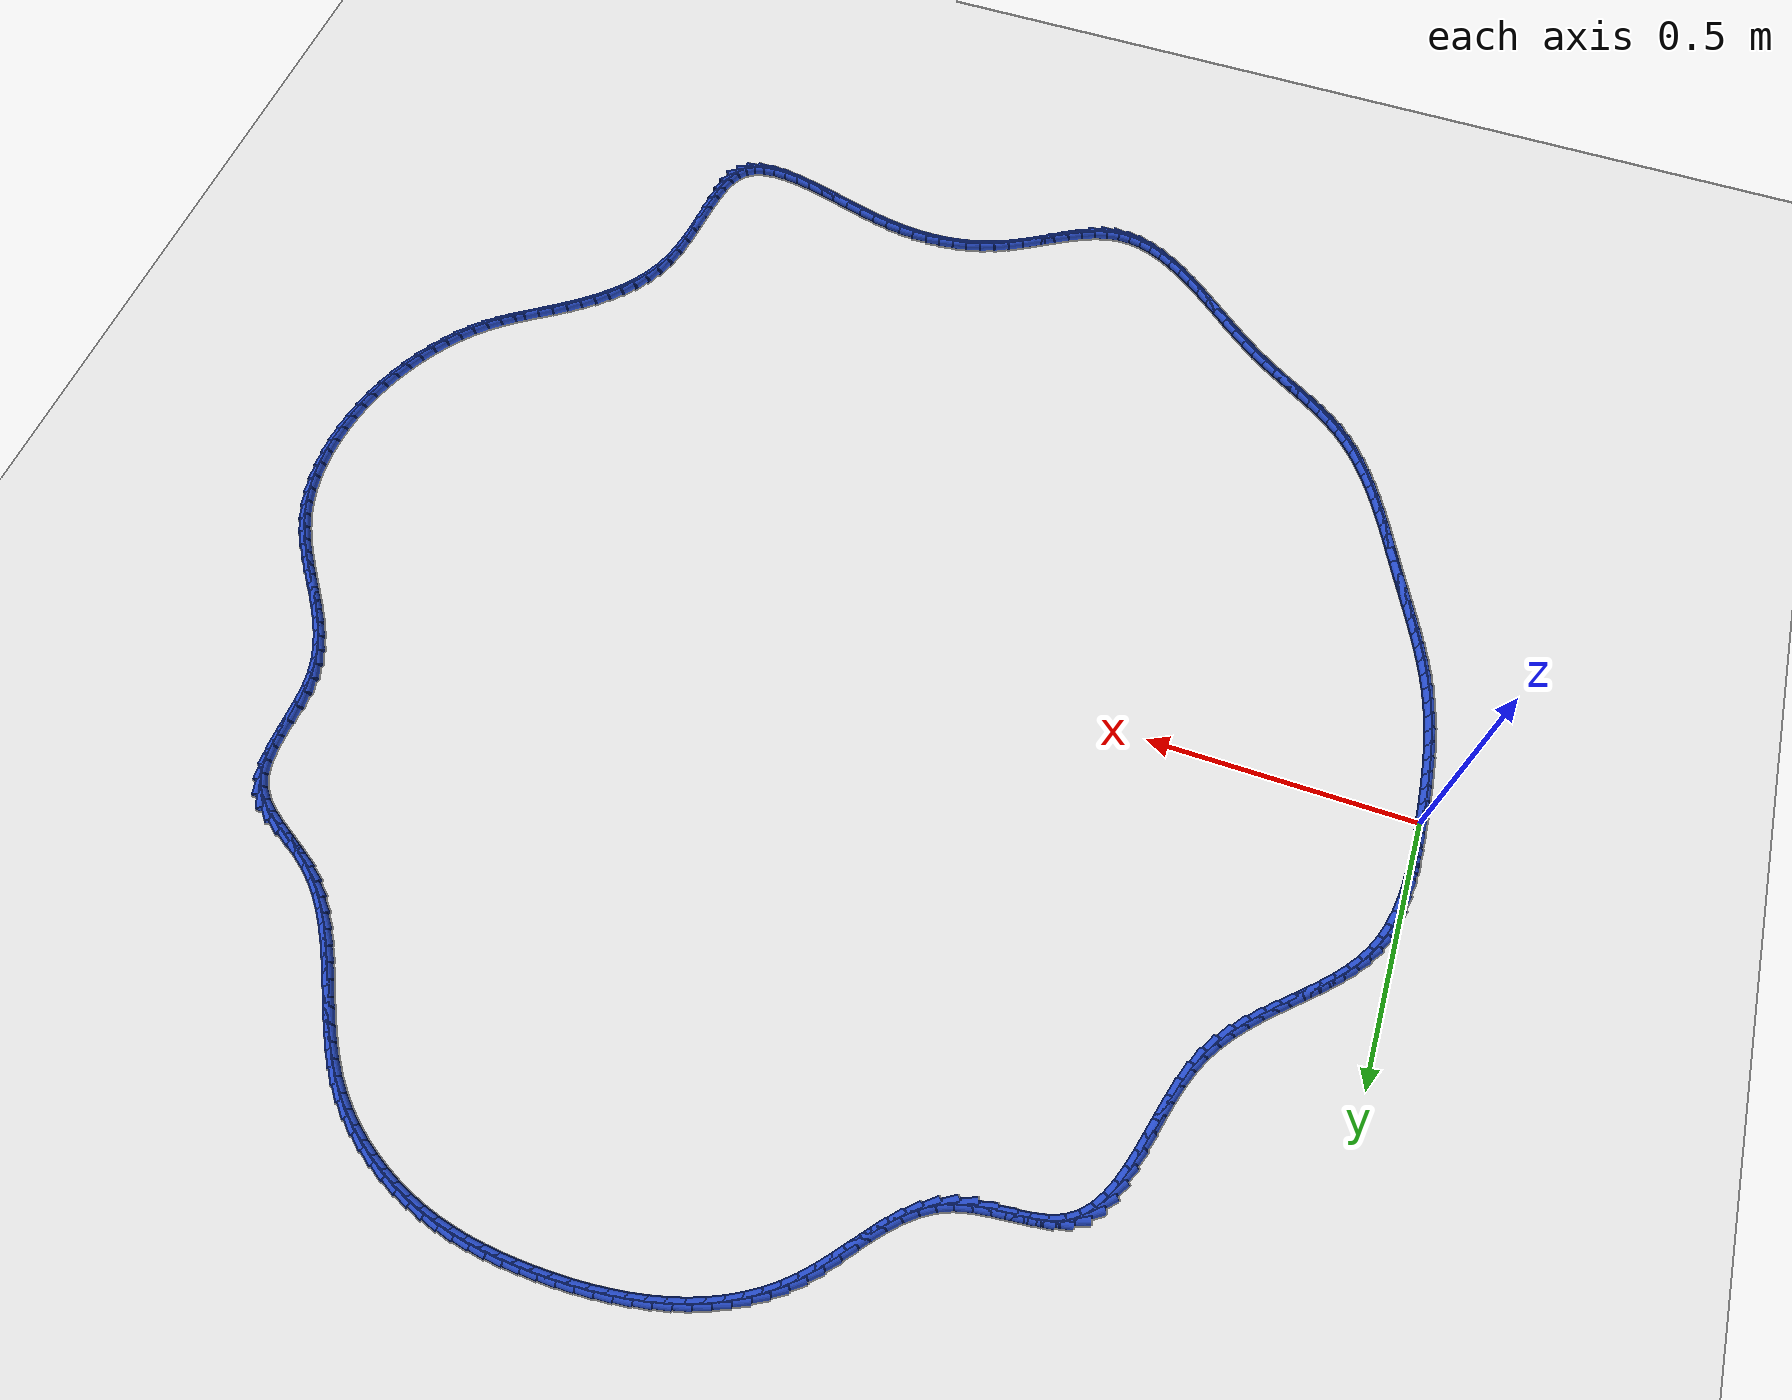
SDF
<sdf version="1.6">
 <world name="default">
  <light name="sun" type="directional">
   <pose>0 0 10 0 -0 0</pose>
   <diffuse>0.8 0.8 0.8 1</diffuse>
   <specular>0.2 0.2 0.2 1</specular>
   <attenuation>
    <range>1000</range>
    <constant>0.9</constant>
    <linear>0.01</linear>
    <quadratic>0.001</quadratic>
   </attenuation>
   <direction>-0.5 0.1 -0.9</direction>
  </light>
  <model name="ground_plane">
   <static>1</static>
   <link name="link">
    <collision name="collision">
     <geometry><plane><normal>0 0 1</normal><size>100 100</size></plane></geometry>
     <surface><friction><ode><mu>100</mu><mu2>50</mu2></ode></friction></surface>
    </collision>
    <visual name="visual">
     <cast_shadows>0</cast_shadows>
     <geometry><plane><normal>0 0 1</normal><size>100 100</size></plane></geometry>
     <material>
      <script><uri>file://media/materials/scripts/gazebo.material</uri><name>Gazebo/WhiteGlow</name></script>
     </material>
    </visual>
   </link>
  </model>
  <gravity>0 0 -9.8</gravity>
  <magnetic_field>6e-06 2.3e-05 -4.2e-05</magnetic_field>
  <atmosphere type="adiabatic"/>
  <physics name="default_physics" default="0" type="ode">
   <max_step_size>0.001</max_step_size>
   <real_time_factor>1</real_time_factor>
   <real_time_update_rate>1000</real_time_update_rate>
  </physics>
  <scene><ambient>0.4 0.4 0.4 1</ambient><background>0.7 0.7 0.7 1</background><shadows>1</shadows></scene>
  <spherical_coordinates>
   <surface_model>EARTH_WGS84</surface_model>
   <latitude_deg>0</latitude_deg>
   <longitude_deg>0</longitude_deg>
   <elevation>0</elevation>
   <heading_deg>0</heading_deg>
  </spherical_coordinates>
  <model name="line">
   <link name="link_0">
    <pose>4.662069341687669e-18 -8.326672684688674e-17 0.01 0 1.57 -1.539609658872592</pose>
    <collision name="collision">
     <geometry><cylinder><radius>0.01</radius><length>0.08</length></cylinder></geometry>
    </collision>
    <visual name="visual">
     <material>
      <script><name>Gazebo/Blue</name><uri>file://media/materials/scripts/gazebo.material</uri></script>
     </material>
     <geometry><cylinder><radius>0.01</radius><length>0.08</length></cylinder></geometry>
    </visual>
   </link>
   <link name="link_1">
    <pose>-0.000966400616148828 0.03097757312513372 0.01 0 1.57 -1.5587502622924951</pose>
    <collision name="collision">
     <geometry><cylinder><radius>0.01</radius><length>0.08</length></cylinder></geometry>
    </collision>
    <visual name="visual">
     <material>
      <script><name>Gazebo/Blue</name><uri>file://media/materials/scripts/gazebo.material</uri></script>
     </material>
     <geometry><cylinder><radius>0.01</radius><length>0.08</length></cylinder></geometry>
    </visual>
   </link>
   <link name="link_2">
    <pose>-0.001340816626458476 0.062058089076894654 0.01 0 1.57 1.5545285447388046</pose>
    <collision name="collision">
     <geometry><cylinder><radius>0.01</radius><length>0.08</length></cylinder></geometry>
    </collision>
    <visual name="visual">
     <material>
      <script><name>Gazebo/Blue</name><uri>file://media/materials/scripts/gazebo.material</uri></script>
     </material>
     <geometry><cylinder><radius>0.01</radius><length>0.08</length></cylinder></geometry>
    </visual>
   </link>
   <link name="link_3">
    <pose>-0.0008371086384844982 0.09301888948408303 0.01 0 1.57 1.5163740549494504</pose>
    <collision name="collision">
     <geometry><cylinder><radius>0.01</radius><length>0.08</length></cylinder></geometry>
    </collision>
    <visual name="visual">
     <material>
      <script><name>Gazebo/Blue</name><uri>file://media/materials/scripts/gazebo.material</uri></script>
     </material>
     <geometry><cylinder><radius>0.01</radius><length>0.08</length></cylinder></geometry>
    </visual>
   </link>
   <link name="link_4">
    <pose>0.0008308627402175395 0.12363731597549919 0.01 0 1.57 1.467405186007337</pose>
    <collision name="collision">
     <geometry><cylinder><radius>0.01</radius><length>0.08</length></cylinder></geometry>
    </collision>
    <visual name="visual">
     <material>
      <script><name>Gazebo/Blue</name><uri>file://media/materials/scripts/gazebo.material</uri></script>
     </material>
     <geometry><cylinder><radius>0.01</radius><length>0.08</length></cylinder></geometry>
    </visual>
   </link>
   <link name="link_5">
    <pose>0.0039492369020920765 0.15369071017994346 0.01 0 1.57 1.4064024631591359</pose>
    <collision name="collision">
     <geometry><cylinder><radius>0.01</radius><length>0.08</length></cylinder></geometry>
    </collision>
    <visual name="visual">
     <material>
      <script><name>Gazebo/Blue</name><uri>file://media/materials/scripts/gazebo.material</uri></script>
     </material>
     <geometry><cylinder><radius>0.01</radius><length>0.08</length></cylinder></geometry>
    </visual>
   </link>
   <link name="link_6">
    <pose>0.008804153239583558 0.18295641372621615 0.01 0 1.57 1.332030836499823</pose>
    <collision name="collision">
     <geometry><cylinder><radius>0.01</radius><length>0.08</length></cylinder></geometry>
    </collision>
    <visual name="visual">
     <material>
      <script><name>Gazebo/Blue</name><uri>file://media/materials/scripts/gazebo.material</uri></script>
     </material>
     <geometry><cylinder><radius>0.01</radius><length>0.08</length></cylinder></geometry>
    </visual>
   </link>
   <link name="link_7">
    <pose>0.01568175114513641 0.21121176824311758 0.01 0 1.57 1.2430969351232288</pose>
    <collision name="collision">
     <geometry><cylinder><radius>0.01</radius><length>0.08</length></cylinder></geometry>
    </collision>
    <visual name="visual">
     <material>
      <script><name>Gazebo/Blue</name><uri>file://media/materials/scripts/gazebo.material</uri></script>
     </material>
     <geometry><cylinder><radius>0.01</radius><length>0.08</length></cylinder></geometry>
    </visual>
   </link>
   <link name="link_8">
    <pose>0.024868170011195075 0.23823411535944805 0.01 0 1.57 1.1390304636194675</pose>
    <collision name="collision">
     <geometry><cylinder><radius>0.01</radius><length>0.08</length></cylinder></geometry>
    </collision>
    <visual name="visual">
     <material>
      <script><name>Gazebo/Blue</name><uri>file://media/materials/scripts/gazebo.material</uri></script>
     </material>
     <geometry><cylinder><radius>0.01</radius><length>0.08</length></cylinder></geometry>
    </visual>
   </link>
   <link name="link_9">
    <pose>0.03664859619295909 0.26380149346409615 0.01 0 1.57 1.0293367742738542</pose>
    <collision name="collision">
     <geometry><cylinder><radius>0.01</radius><length>0.08</length></cylinder></geometry>
    </collision>
    <visual name="visual">
     <material>
      <script><name>Gazebo/Blue</name><uri>file://media/materials/scripts/gazebo.material</uri></script>
     </material>
     <geometry><cylinder><radius>0.01</radius><length>0.08</length></cylinder></geometry>
    </visual>
   </link>
   <link name="link_10">
    <pose>0.05110571576127611 0.28783998774764086 0.01 0 1.57 0.936071537319956</pose>
    <collision name="collision">
     <geometry><cylinder><radius>0.01</radius><length>0.08</length></cylinder></geometry>
    </collision>
    <visual name="visual">
     <material>
      <script><name>Gazebo/Blue</name><uri>file://media/materials/scripts/gazebo.material</uri></script>
     </material>
     <geometry><cylinder><radius>0.01</radius><length>0.08</length></cylinder></geometry>
    </visual>
   </link>
   <link name="link_11">
    <pose>0.06787018557350744 0.31060615937772645 0.01 0 1.57 0.8632363737783122</pose>
    <collision name="collision">
     <geometry><cylinder><radius>0.01</radius><length>0.08</length></cylinder></geometry>
    </collision>
    <visual name="visual">
     <material>
      <script><name>Gazebo/Blue</name><uri>file://media/materials/scripts/gazebo.material</uri></script>
     </material>
     <geometry><cylinder><radius>0.01</radius><length>0.08</length></cylinder></geometry>
    </visual>
   </link>
   <link name="link_12">
    <pose>0.08651146518915179 0.3324013105170515 0.01 0 1.57 0.8105762616773072</pose>
    <collision name="collision">
     <geometry><cylinder><radius>0.01</radius><length>0.08</length></cylinder></geometry>
    </collision>
    <visual name="visual">
     <material>
      <script><name>Gazebo/Blue</name><uri>file://media/materials/scripts/gazebo.material</uri></script>
     </material>
     <geometry><cylinder><radius>0.01</radius><length>0.08</length></cylinder></geometry>
    </visual>
   </link>
   <link name="link_13">
    <pose>0.10659901416770784 0.3535267433283146 0.01 0 1.57 0.7771265216971788</pose>
    <collision name="collision">
     <geometry><cylinder><radius>0.01</radius><length>0.08</length></cylinder></geometry>
    </collision>
    <visual name="visual">
     <material>
      <script><name>Gazebo/Blue</name><uri>file://media/materials/scripts/gazebo.material</uri></script>
     </material>
     <geometry><cylinder><radius>0.01</radius><length>0.08</length></cylinder></geometry>
    </visual>
   </link>
   <link name="link_14">
    <pose>0.12770229206867434 0.3742837599742141 0.01 0 1.57 0.7618394701901783</pose>
    <collision name="collision">
     <geometry><cylinder><radius>0.01</radius><length>0.08</length></cylinder></geometry>
    </collision>
    <visual name="visual">
     <material>
      <script><name>Gazebo/Blue</name><uri>file://media/materials/scripts/gazebo.material</uri></script>
     </material>
     <geometry><cylinder><radius>0.01</radius><length>0.08</length></cylinder></geometry>
    </visual>
   </link>
   <link name="link_15">
    <pose>0.14939075845154995 0.39497366261744865 0.01 0 1.57 0.7639124901062196</pose>
    <collision name="collision">
     <geometry><cylinder><radius>0.01</radius><length>0.08</length></cylinder></geometry>
    </collision>
    <visual name="visual">
     <material>
      <script><name>Gazebo/Blue</name><uri>file://media/materials/scripts/gazebo.material</uri></script>
     </material>
     <geometry><cylinder><radius>0.01</radius><length>0.08</length></cylinder></geometry>
    </visual>
   </link>
   <link name="link_16">
    <pose>0.17123387287583336 0.4158977534207168 0.01 0 1.57 0.782896451284364</pose>
    <collision name="collision">
     <geometry><cylinder><radius>0.01</radius><length>0.08</length></cylinder></geometry>
    </collision>
    <visual name="visual">
     <material>
      <script><name>Gazebo/Blue</name><uri>file://media/materials/scripts/gazebo.material</uri></script>
     </material>
     <geometry><cylinder><radius>0.01</radius><length>0.08</length></cylinder></geometry>
    </visual>
   </link>
   <link name="link_17">
    <pose>0.19280109490102337 0.43735733454671694 0.01 0 1.57 0.8186500083368146</pose>
    <collision name="collision">
     <geometry><cylinder><radius>0.01</radius><length>0.08</length></cylinder></geometry>
    </collision>
    <visual name="visual">
     <material>
      <script><name>Gazebo/Blue</name><uri>file://media/materials/scripts/gazebo.material</uri></script>
     </material>
     <geometry><cylinder><radius>0.01</radius><length>0.08</length></cylinder></geometry>
    </visual>
   </link>
   <link name="link_18">
    <pose>0.21366188408661854 0.45965370815814766 0.01 0 1.57 0.8711649982706587</pose>
    <collision name="collision">
     <geometry><cylinder><radius>0.01</radius><length>0.08</length></cylinder></geometry>
    </collision>
    <visual name="visual">
     <material>
      <script><name>Gazebo/Blue</name><uri>file://media/materials/scripts/gazebo.material</uri></script>
     </material>
     <geometry><cylinder><radius>0.01</radius><length>0.08</length></cylinder></geometry>
    </visual>
   </link>
   <link name="link_19">
    <pose>0.23338569999211778 0.4830881764177077 0.01 0 1.57 0.9402610401511503</pose>
    <collision name="collision">
     <geometry><cylinder><radius>0.01</radius><length>0.08</length></cylinder></geometry>
    </collision>
    <visual name="visual">
     <material>
      <script><name>Gazebo/Blue</name><uri>file://media/materials/scripts/gazebo.material</uri></script>
     </material>
     <geometry><cylinder><radius>0.01</radius><length>0.08</length></cylinder></geometry>
    </visual>
   </link>
   <link name="link_20">
    <pose>0.25154200217701955 0.5079620414880951 0.01 0 1.57 1.0251575916252154</pose>
    <collision name="collision">
     <geometry><cylinder><radius>0.01</radius><length>0.08</length></cylinder></geometry>
    </collision>
    <visual name="visual">
     <material>
      <script><name>Gazebo/Blue</name><uri>file://media/materials/scripts/gazebo.material</uri></script>
     </material>
     <geometry><cylinder><radius>0.01</radius><length>0.08</length></cylinder></geometry>
    </visual>
   </link>
   <link name="link_21">
    <pose>0.2677002502008228 0.5345766055320087 0.01 0 1.57 1.122738086164052</pose>
    <collision name="collision">
     <geometry><cylinder><radius>0.01</radius><length>0.08</length></cylinder></geometry>
    </collision>
    <visual name="visual">
     <material>
      <script><name>Gazebo/Blue</name><uri>file://media/materials/scripts/gazebo.material</uri></script>
     </material>
     <geometry><cylinder><radius>0.01</radius><length>0.08</length></cylinder></geometry>
    </visual>
   </link>
   <link name="link_22">
    <pose>0.281460899666437 0.5632051147447366 0.01 0 1.57 1.209706868842813</pose>
    <collision name="collision">
     <geometry><cylinder><radius>0.01</radius><length>0.08</length></cylinder></geometry>
    </collision>
    <visual name="visual">
     <material>
      <script><name>Gazebo/Blue</name><uri>file://media/materials/scripts/gazebo.material</uri></script>
     </material>
     <geometry><cylinder><radius>0.01</radius><length>0.08</length></cylinder></geometry>
    </visual>
   </link>
   <link name="link_23">
    <pose>0.29295481800520595 0.5936407147882385 0.01 0 1.57 1.270271027608506</pose>
    <collision name="collision">
     <geometry><cylinder><radius>0.01</radius><length>0.08</length></cylinder></geometry>
    </collision>
    <visual name="visual">
     <material>
      <script><name>Gazebo/Blue</name><uri>file://media/materials/scripts/gazebo.material</uri></script>
     </material>
     <geometry><cylinder><radius>0.01</radius><length>0.08</length></cylinder></geometry>
    </visual>
   </link>
   <link name="link_24">
    <pose>0.3027581874149358 0.6252734761187259 0.01 0 1.57 1.3068878999838809</pose>
    <collision name="collision">
     <geometry><cylinder><radius>0.01</radius><length>0.08</length></cylinder></geometry>
    </collision>
    <visual name="visual">
     <material>
      <script><name>Gazebo/Blue</name><uri>file://media/materials/scripts/gazebo.material</uri></script>
     </material>
     <geometry><cylinder><radius>0.01</radius><length>0.08</length></cylinder></geometry>
    </visual>
   </link>
   <link name="link_25">
    <pose>0.31146100340579586 0.6574809661178608 0.01 0 1.57 1.321365160492764</pose>
    <collision name="collision">
     <geometry><cylinder><radius>0.01</radius><length>0.08</length></cylinder></geometry>
    </collision>
    <visual name="visual">
     <material>
      <script><name>Gazebo/Blue</name><uri>file://media/materials/scripts/gazebo.material</uri></script>
     </material>
     <geometry><cylinder><radius>0.01</radius><length>0.08</length></cylinder></geometry>
    </visual>
   </link>
   <link name="link_26">
    <pose>0.31965326148795503 0.6896407521673056 0.01 0 1.57 1.313919769041572</pose>
    <collision name="collision">
     <geometry><cylinder><radius>0.01</radius><length>0.08</length></cylinder></geometry>
    </collision>
    <visual name="visual">
     <material>
      <script><name>Gazebo/Blue</name><uri>file://media/materials/scripts/gazebo.material</uri></script>
     </material>
     <geometry><cylinder><radius>0.01</radius><length>0.08</length></cylinder></geometry>
    </visual>
   </link>
   <link name="link_27">
    <pose>0.32792495717158254 0.7211304016487228 0.01 0 1.57 1.2829282449685524</pose>
    <collision name="collision">
     <geometry><cylinder><radius>0.01</radius><length>0.08</length></cylinder></geometry>
    </collision>
    <visual name="visual">
     <material>
      <script><name>Gazebo/Blue</name><uri>file://media/materials/scripts/gazebo.material</uri></script>
     </material>
     <geometry><cylinder><radius>0.01</radius><length>0.08</length></cylinder></geometry>
    </visual>
   </link>
   <link name="link_28">
    <pose>0.3368660859668477 0.751327481943775 0.01 0 1.57 1.224645860056994</pose>
    <collision name="collision">
     <geometry><cylinder><radius>0.01</radius><length>0.08</length></cylinder></geometry>
    </collision>
    <visual name="visual">
     <material>
      <script><name>Gazebo/Blue</name><uri>file://media/materials/scripts/gazebo.material</uri></script>
     </material>
     <geometry><cylinder><radius>0.01</radius><length>0.08</length></cylinder></geometry>
    </visual>
   </link>
   <link name="link_29">
    <pose>0.34706664338391935 0.779609560434124 0.01 0 1.57 1.133027419413509</pose>
    <collision name="collision">
     <geometry><cylinder><radius>0.01</radius><length>0.08</length></cylinder></geometry>
    </collision>
    <visual name="visual">
     <material>
      <script><name>Gazebo/Blue</name><uri>file://media/materials/scripts/gazebo.material</uri></script>
     </material>
     <geometry><cylinder><radius>0.01</radius><length>0.08</length></cylinder></geometry>
    </visual>
   </link>
   <link name="link_30">
    <pose>0.359116624932967 0.8053542045014328 0.01 0 1.57 1.0003799940282918</pose>
    <collision name="collision">
     <geometry><cylinder><radius>0.01</radius><length>0.08</length></cylinder></geometry>
    </collision>
    <visual name="visual">
     <material>
      <script><name>Gazebo/Blue</name><uri>file://media/materials/scripts/gazebo.material</uri></script>
     </material>
     <geometry><cylinder><radius>0.01</radius><length>0.08</length></cylinder></geometry>
    </visual>
   </link>
   <link name="link_31">
    <pose>0.3736060261241594 0.8279389815273631 0.01 0 1.57 0.8207252908671735</pose>
    <collision name="collision">
     <geometry><cylinder><radius>0.01</radius><length>0.08</length></cylinder></geometry>
    </collision>
    <visual name="visual">
     <material>
      <script><name>Gazebo/Blue</name><uri>file://media/materials/scripts/gazebo.material</uri></script>
     </material>
     <geometry><cylinder><radius>0.01</radius><length>0.08</length></cylinder></geometry>
    </visual>
   </link>
   <link name="link_32">
    <pose>0.3911248424676661 0.8467414588935783 0.01 0 1.57 0.5979445767017307</pose>
    <collision name="collision">
     <geometry><cylinder><radius>0.01</radius><length>0.08</length></cylinder></geometry>
    </collision>
    <visual name="visual">
     <material>
      <script><name>Gazebo/Blue</name><uri>file://media/materials/scripts/gazebo.material</uri></script>
     </material>
     <geometry><cylinder><radius>0.01</radius><length>0.08</length></cylinder></geometry>
    </visual>
   </link>
   <link name="link_33">
    <pose>0.412263069473656 0.8611392039817398 0.01 0 1.57 0.3687455745161602</pose>
    <collision name="collision">
     <geometry><cylinder><radius>0.01</radius><length>0.08</length></cylinder></geometry>
    </collision>
    <visual name="visual">
     <material>
      <script><name>Gazebo/Blue</name><uri>file://media/materials/scripts/gazebo.material</uri></script>
     </material>
     <geometry><cylinder><radius>0.01</radius><length>0.08</length></cylinder></geometry>
    </visual>
   </link>
   <link name="link_34">
    <pose>0.4373518358921339 0.8708340232698599 0.01 0 1.57 0.21467041572185866</pose>
    <collision name="collision">
     <geometry><cylinder><radius>0.01</radius><length>0.08</length></cylinder></geometry>
    </collision>
    <visual name="visual">
     <material>
      <script><name>Gazebo/Blue</name><uri>file://media/materials/scripts/gazebo.material</uri></script>
     </material>
     <geometry><cylinder><radius>0.01</radius><length>0.08</length></cylinder></geometry>
    </visual>
   </link>
   <link name="link_35">
    <pose>0.4655594951410916 0.876984137426286 0.01 0 1.57 0.13743042600279587</pose>
    <collision name="collision">
     <geometry><cylinder><radius>0.01</radius><length>0.08</length></cylinder></geometry>
    </collision>
    <visual name="visual">
     <material>
      <script><name>Gazebo/Blue</name><uri>file://media/materials/scripts/gazebo.material</uri></script>
     </material>
     <geometry><cylinder><radius>0.01</radius><length>0.08</length></cylinder></geometry>
    </visual>
   </link>
   <link name="link_36">
    <pose>0.49572806150552584 0.8811565175727589 0.01 0 1.57 0.1208629684910558</pose>
    <collision name="collision">
     <geometry><cylinder><radius>0.01</radius><length>0.08</length></cylinder></geometry>
    </collision>
    <visual name="visual">
     <material>
      <script><name>Gazebo/Blue</name><uri>file://media/materials/scripts/gazebo.material</uri></script>
     </material>
     <geometry><cylinder><radius>0.01</radius><length>0.08</length></cylinder></geometry>
    </visual>
   </link>
   <link name="link_37">
    <pose>0.5266995324904046 0.8849181558485553 0.01 0 1.57 0.1592688564279565</pose>
    <collision name="collision">
     <geometry><cylinder><radius>0.01</radius><length>0.08</length></cylinder></geometry>
    </collision>
    <visual name="visual">
     <material>
      <script><name>Gazebo/Blue</name><uri>file://media/materials/scripts/gazebo.material</uri></script>
     </material>
     <geometry><cylinder><radius>0.01</radius><length>0.08</length></cylinder></geometry>
    </visual>
   </link>
   <link name="link_38">
    <pose>0.5573159056006951 0.8898360443929524 0.01 0 1.57 0.25675725050288645</pose>
    <collision name="collision">
     <geometry><cylinder><radius>0.01</radius><length>0.08</length></cylinder></geometry>
    </collision>
    <visual name="visual">
     <material>
      <script><name>Gazebo/Blue</name><uri>file://media/materials/scripts/gazebo.material</uri></script>
     </material>
     <geometry><cylinder><radius>0.01</radius><length>0.08</length></cylinder></geometry>
    </visual>
   </link>
   <link name="link_39">
    <pose>0.586419178341366 0.8974771753452274 0.01 0 1.57 0.4152905521539522</pose>
    <collision name="collision">
     <geometry><cylinder><radius>0.01</radius><length>0.08</length></cylinder></geometry>
    </collision>
    <visual name="visual">
     <material>
      <script><name>Gazebo/Blue</name><uri>file://media/materials/scripts/gazebo.material</uri></script>
     </material>
     <geometry><cylinder><radius>0.01</radius><length>0.08</length></cylinder></geometry>
    </visual>
   </link>
   <link name="link_40">
    <pose>0.6130014569415652 0.909198251509453 0.01 0 1.57 0.5766440587714</pose>
    <collision name="collision">
     <geometry><cylinder><radius>0.01</radius><length>0.08</length></cylinder></geometry>
    </collision>
    <visual name="visual">
     <material>
      <script><name>Gazebo/Blue</name><uri>file://media/materials/scripts/gazebo.material</uri></script>
     </material>
     <geometry><cylinder><radius>0.01</radius><length>0.08</length></cylinder></geometry>
    </visual>
   </link>
   <link name="link_41">
    <pose>0.6371098892201381 0.9248779537045021 0.01 0 1.57 0.7063062705090236</pose>
    <collision name="collision">
     <geometry><cylinder><radius>0.01</radius><length>0.08</length></cylinder></geometry>
    </collision>
    <visual name="visual">
     <material>
      <script><name>Gazebo/Blue</name><uri>file://media/materials/scripts/gazebo.material</uri></script>
     </material>
     <geometry><cylinder><radius>0.01</radius><length>0.08</length></cylinder></geometry>
    </visual>
   </link>
   <link name="link_42">
    <pose>0.6592440332665317 0.9437611751025716 0.01 0 1.57 0.8013067904103504</pose>
    <collision name="collision">
     <geometry><cylinder><radius>0.01</radius><length>0.08</length></cylinder></geometry>
    </collision>
    <visual name="visual">
     <material>
      <script><name>Gazebo/Blue</name><uri>file://media/materials/scripts/gazebo.material</uri></script>
     </material>
     <geometry><cylinder><radius>0.01</radius><length>0.08</length></cylinder></geometry>
    </visual>
   </link>
   <link name="link_43">
    <pose>0.6799051776078241 0.965090384682453 0.01 0 1.57 0.8631725897219779</pose>
    <collision name="collision">
     <geometry><cylinder><radius>0.01</radius><length>0.08</length></cylinder></geometry>
    </collision>
    <visual name="visual">
     <material>
      <script><name>Gazebo/Blue</name><uri>file://media/materials/scripts/gazebo.material</uri></script>
     </material>
     <geometry><cylinder><radius>0.01</radius><length>0.08</length></cylinder></geometry>
    </visual>
   </link>
   <link name="link_44">
    <pose>0.6995946107710933 0.9881080514229378 0.01 0 1.57 0.8945261285083662</pose>
    <collision name="collision">
     <geometry><cylinder><radius>0.01</radius><length>0.08</length></cylinder></geometry>
    </collision>
    <visual name="visual">
     <material>
      <script><name>Gazebo/Blue</name><uri>file://media/materials/scripts/gazebo.material</uri></script>
     </material>
     <geometry><cylinder><radius>0.01</radius><length>0.08</length></cylinder></geometry>
    </visual>
   </link>
   <link name="link_45">
    <pose>0.7188136212834179 1.012056644302818 0.01 0 1.57 0.8972626645847869</pose>
    <collision name="collision">
     <geometry><cylinder><radius>0.01</radius><length>0.08</length></cylinder></geometry>
    </collision>
    <visual name="visual">
     <material>
      <script><name>Gazebo/Blue</name><uri>file://media/materials/scripts/gazebo.material</uri></script>
     </material>
     <geometry><cylinder><radius>0.01</radius><length>0.08</length></cylinder></geometry>
    </visual>
   </link>
   <link name="link_46">
    <pose>0.7380634976718757 1.0361786323008855 0.01 0 1.57 0.8718816124382054</pose>
    <collision name="collision">
     <geometry><cylinder><radius>0.01</radius><length>0.08</length></cylinder></geometry>
    </collision>
    <visual name="visual">
     <material>
      <script><name>Gazebo/Blue</name><uri>file://media/materials/scripts/gazebo.material</uri></script>
     </material>
     <geometry><cylinder><radius>0.01</radius><length>0.08</length></cylinder></geometry>
    </visual>
   </link>
   <link name="link_47">
    <pose>0.7578455284635457 1.0597164843959321 0.01 0 1.57 0.8174880087761471</pose>
    <collision name="collision">
     <geometry><cylinder><radius>0.01</radius><length>0.08</length></cylinder></geometry>
    </collision>
    <visual name="visual">
     <material>
      <script><name>Gazebo/Blue</name><uri>file://media/materials/scripts/gazebo.material</uri></script>
     </material>
     <geometry><cylinder><radius>0.01</radius><length>0.08</length></cylinder></geometry>
    </visual>
   </link>
   <link name="link_48">
    <pose>0.7786610021855057 1.0819126695667496 0.01 0 1.57 0.7368810352955288</pose>
    <collision name="collision">
     <geometry><cylinder><radius>0.01</radius><length>0.08</length></cylinder></geometry>
    </collision>
    <visual name="visual">
     <material>
      <script><name>Gazebo/Blue</name><uri>file://media/materials/scripts/gazebo.material</uri></script>
     </material>
     <geometry><cylinder><radius>0.01</radius><length>0.08</length></cylinder></geometry>
    </visual>
   </link>
   <link name="link_49">
    <pose>0.8009296575185593 1.1021189447791633 0.01 0 1.57 0.6525785681016388</pose>
    <collision name="collision">
     <geometry><cylinder><radius>0.01</radius><length>0.08</length></cylinder></geometry>
    </collision>
    <visual name="visual">
     <material>
      <script><name>Gazebo/Blue</name><uri>file://media/materials/scripts/gazebo.material</uri></script>
     </material>
     <geometry><cylinder><radius>0.01</radius><length>0.08</length></cylinder></geometry>
    </visual>
   </link>
   <link name="link_50">
    <pose>0.8246517210558207 1.1202492707761358 0.01 0 1.57 0.5727690395097536</pose>
    <collision name="collision">
     <geometry><cylinder><radius>0.01</radius><length>0.08</length></cylinder></geometry>
    </collision>
    <visual name="visual">
     <material>
      <script><name>Gazebo/Blue</name><uri>file://media/materials/scripts/gazebo.material</uri></script>
     </material>
     <geometry><cylinder><radius>0.01</radius><length>0.08</length></cylinder></geometry>
    </visual>
   </link>
   <link name="link_51">
    <pose>0.8496929009402826 1.136397881486958 0.01 0 1.57 0.4980572703767897</pose>
    <collision name="collision">
     <geometry><cylinder><radius>0.01</radius><length>0.08</length></cylinder></geometry>
    </collision>
    <visual name="visual">
     <material>
      <script><name>Gazebo/Blue</name><uri>file://media/materials/scripts/gazebo.material</uri></script>
     </material>
     <geometry><cylinder><radius>0.01</radius><length>0.08</length></cylinder></geometry>
    </visual>
   </link>
   <link name="link_52">
    <pose>0.8759188435826526 1.1506590935706593 0.01 0 1.57 0.42874590464454415</pose>
    <collision name="collision">
     <geometry><cylinder><radius>0.01</radius><length>0.08</length></cylinder></geometry>
    </collision>
    <visual name="visual">
     <material>
      <script><name>Gazebo/Blue</name><uri>file://media/materials/scripts/gazebo.material</uri></script>
     </material>
     <geometry><cylinder><radius>0.01</radius><length>0.08</length></cylinder></geometry>
    </visual>
   </link>
   <link name="link_53">
    <pose>0.9031951953936375 1.1631272236862666 0.01 0 1.57 0.3648893159389845</pose>
    <collision name="collision">
     <geometry><cylinder><radius>0.01</radius><length>0.08</length></cylinder></geometry>
    </collision>
    <visual name="visual">
     <material>
      <script><name>Gazebo/Blue</name><uri>file://media/materials/scripts/gazebo.material</uri></script>
     </material>
     <geometry><cylinder><radius>0.01</radius><length>0.08</length></cylinder></geometry>
    </visual>
   </link>
   <link name="link_54">
    <pose>0.9313876027839454 1.1738965884928092 0.01 0 1.57 0.3063557530333242</pose>
    <collision name="collision">
     <geometry><cylinder><radius>0.01</radius><length>0.08</length></cylinder></geometry>
    </collision>
    <visual name="visual">
     <material>
      <script><name>Gazebo/Blue</name><uri>file://media/materials/scripts/gazebo.material</uri></script>
     </material>
     <geometry><cylinder><radius>0.01</radius><length>0.08</length></cylinder></geometry>
    </visual>
   </link>
   <link name="link_55">
    <pose>0.9603617121642831 1.1830615046493143 0.01 0 1.57 0.25288775787532736</pose>
    <collision name="collision">
     <geometry><cylinder><radius>0.01</radius><length>0.08</length></cylinder></geometry>
    </collision>
    <visual name="visual">
     <material>
      <script><name>Gazebo/Blue</name><uri>file://media/materials/scripts/gazebo.material</uri></script>
     </material>
     <geometry><cylinder><radius>0.01</radius><length>0.08</length></cylinder></geometry>
    </visual>
   </link>
   <link name="link_56">
    <pose>0.9899831699453584 1.1907162888148093 0.01 0 1.57 0.20415336437988826</pose>
    <collision name="collision">
     <geometry><cylinder><radius>0.01</radius><length>0.08</length></cylinder></geometry>
    </collision>
    <visual name="visual">
     <material>
      <script><name>Gazebo/Blue</name><uri>file://media/materials/scripts/gazebo.material</uri></script>
     </material>
     <geometry><cylinder><radius>0.01</radius><length>0.08</length></cylinder></geometry>
    </visual>
   </link>
   <link name="link_57">
    <pose>1.0201176225378776 1.1969552576483231 0.01 0 1.57 0.15978546220421058</pose>
    <collision name="collision">
     <geometry><cylinder><radius>0.01</radius><length>0.08</length></cylinder></geometry>
    </collision>
    <visual name="visual">
     <material>
      <script><name>Gazebo/Blue</name><uri>file://media/materials/scripts/gazebo.material</uri></script>
     </material>
     <geometry><cylinder><radius>0.01</radius><length>0.08</length></cylinder></geometry>
    </visual>
   </link>
   <link name="link_58">
    <pose>1.0506307163525497 1.2018727278088837 0.01 0 1.57 0.11940977143722892</pose>
    <collision name="collision">
     <geometry><cylinder><radius>0.01</radius><length>0.08</length></cylinder></geometry>
    </collision>
    <visual name="visual">
     <material>
      <script><name>Gazebo/Blue</name><uri>file://media/materials/scripts/gazebo.material</uri></script>
     </material>
     <geometry><cylinder><radius>0.01</radius><length>0.08</length></cylinder></geometry>
    </visual>
   </link>
   <link name="link_59">
    <pose>1.081388097800081 1.2055630159555188 0.01 0 1.57 0.08266332678488861</pose>
    <collision name="collision">
     <geometry><cylinder><radius>0.01</radius><length>0.08</length></cylinder></geometry>
    </collision>
    <visual name="visual">
     <material>
      <script><name>Gazebo/Blue</name><uri>file://media/materials/scripts/gazebo.material</uri></script>
     </material>
     <geometry><cylinder><radius>0.01</radius><length>0.08</length></cylinder></geometry>
    </visual>
   </link>
   <link name="link_60">
    <pose>1.1122554132911793 1.2081204387472564 0.01 0 1.57 0.0492057576129428</pose>
    <collision name="collision">
     <geometry><cylinder><radius>0.01</radius><length>0.08</length></cylinder></geometry>
    </collision>
    <visual name="visual">
     <material>
      <script><name>Gazebo/Blue</name><uri>file://media/materials/scripts/gazebo.material</uri></script>
     </material>
     <geometry><cylinder><radius>0.01</radius><length>0.08</length></cylinder></geometry>
    </visual>
   </link>
   <link name="link_61">
    <pose>1.1430983092365512 1.2096393128431242 0.01 0 1.57 0.018725478846581253</pose>
    <collision name="collision">
     <geometry><cylinder><radius>0.01</radius><length>0.08</length></cylinder></geometry>
    </collision>
    <visual name="visual">
     <material>
      <script><name>Gazebo/Blue</name><uri>file://media/materials/scripts/gazebo.material</uri></script>
     </material>
     <geometry><cylinder><radius>0.01</radius><length>0.08</length></cylinder></geometry>
    </visual>
   </link>
   <link name="link_62">
    <pose>1.173782432046905 1.210213954902151 0.01 0 1.57 -0.009177796634765499</pose>
    <collision name="collision">
     <geometry><cylinder><radius>0.01</radius><length>0.08</length></cylinder></geometry>
    </collision>
    <visual name="visual">
     <material>
      <script><name>Gazebo/Blue</name><uri>file://media/materials/scripts/gazebo.material</uri></script>
     </material>
     <geometry><cylinder><radius>0.01</radius><length>0.08</length></cylinder></geometry>
    </visual>
   </link>
   <link name="link_63">
    <pose>1.2041758548206851 1.2099350024166173 0.01 0 1.57 -0.03832187731914051</pose>
    <collision name="collision">
     <geometry><cylinder><radius>0.01</radius><length>0.08</length></cylinder></geometry>
    </collision>
    <visual name="visual">
     <material>
      <script><name>Gazebo/Blue</name><uri>file://media/materials/scripts/gazebo.material</uri></script>
     </material>
     <geometry><cylinder><radius>0.01</radius><length>0.08</length></cylinder></geometry>
    </visual>
   </link>
   <link name="link_64">
    <pose>1.2342191849503243 1.2087831216788472 0.01 0 1.57 -0.07290484373197678</pose>
    <collision name="collision">
     <geometry><cylinder><radius>0.01</radius><length>0.08</length></cylinder></geometry>
    </collision>
    <visual name="visual">
     <material>
      <script><name>Gazebo/Blue</name><uri>file://media/materials/scripts/gazebo.material</uri></script>
     </material>
     <geometry><cylinder><radius>0.01</radius><length>0.08</length></cylinder></geometry>
    </visual>
   </link>
   <link name="link_65">
    <pose>1.2639362843348296 1.20661275457769 0.01 0 1.57 -0.11309248596938216</pose>
    <collision name="collision">
     <geometry><cylinder><radius>0.01</radius><length>0.08</length></cylinder></geometry>
    </collision>
    <visual name="visual">
     <material>
      <script><name>Gazebo/Blue</name><uri>file://media/materials/scripts/gazebo.material</uri></script>
     </material>
     <geometry><cylinder><radius>0.01</radius><length>0.08</length></cylinder></geometry>
    </visual>
   </link>
   <link name="link_66">
    <pose>1.2933555983820895 1.203271393820525 0.01 0 1.57 -0.1586842238111268</pose>
    <collision name="collision">
     <geometry><cylinder><radius>0.01</radius><length>0.08</length></cylinder></geometry>
    </collision>
    <visual name="visual">
     <material>
      <script><name>Gazebo/Blue</name><uri>file://media/materials/scripts/gazebo.material</uri></script>
     </material>
     <geometry><cylinder><radius>0.01</radius><length>0.08</length></cylinder></geometry>
    </visual>
   </link>
   <link name="link_67">
    <pose>1.3225055724999917 1.1986065321147334 0.01 0 1.57 -0.20930895600061797</pose>
    <collision name="collision">
     <geometry><cylinder><radius>0.01</radius><length>0.08</length></cylinder></geometry>
    </collision>
    <visual name="visual">
     <material>
      <script><name>Gazebo/Blue</name><uri>file://media/materials/scripts/gazebo.material</uri></script>
     </material>
     <geometry><cylinder><radius>0.01</radius><length>0.08</length></cylinder></geometry>
    </visual>
   </link>
   <link name="link_68">
    <pose>1.3514146520964248 1.1924656621676955 0.01 0 1.57 -0.2643771519026189</pose>
    <collision name="collision">
     <geometry><cylinder><radius>0.01</radius><length>0.08</length></cylinder></geometry>
    </collision>
    <visual name="visual">
     <material>
      <script><name>Gazebo/Blue</name><uri>file://media/materials/scripts/gazebo.material</uri></script>
     </material>
     <geometry><cylinder><radius>0.01</radius><length>0.08</length></cylinder></geometry>
    </visual>
   </link>
   <link name="link_69">
    <pose>1.3801099912257777 1.184697433638929 0.01 0 1.57 -0.32176665142718436</pose>
    <collision name="collision">
     <geometry><cylinder><radius>0.01</radius><length>0.08</length></cylinder></geometry>
    </collision>
    <visual name="visual">
     <material>
      <script><name>Gazebo/Blue</name><uri>file://media/materials/scripts/gazebo.material</uri></script>
     </material>
     <geometry><cylinder><radius>0.01</radius><length>0.08</length></cylinder></geometry>
    </visual>
   </link>
   <link name="link_70">
    <pose>1.4085414026123495 1.1752197879947905 0.01 0 1.57 -0.3793601810932405</pose>
    <collision name="collision">
     <geometry><cylinder><radius>0.01</radius><length>0.08</length></cylinder></geometry>
    </collision>
    <visual name="visual">
     <material>
      <script><name>Gazebo/Blue</name><uri>file://media/materials/scripts/gazebo.material</uri></script>
     </material>
     <geometry><cylinder><radius>0.01</radius><length>0.08</length></cylinder></geometry>
    </visual>
   </link>
   <link name="link_71">
    <pose>1.436538900280601 1.1640579970043168 0.01 0 1.57 -0.4376032993258086</pose>
    <collision name="collision">
     <geometry><cylinder><radius>0.01</radius><length>0.08</length></cylinder></geometry>
    </collision>
    <visual name="visual">
     <material>
      <script><name>Gazebo/Blue</name><uri>file://media/materials/scripts/gazebo.material</uri></script>
     </material>
     <geometry><cylinder><radius>0.01</radius><length>0.08</length></cylinder></geometry>
    </visual>
   </link>
   <link name="link_72">
    <pose>1.4639222023772234 1.1512465567409733 0.01 0 1.57 -0.4971294727617896</pose>
    <collision name="collision">
     <geometry><cylinder><radius>0.01</radius><length>0.08</length></cylinder></geometry>
    </collision>
    <visual name="visual">
     <material>
      <script><name>Gazebo/Blue</name><uri>file://media/materials/scripts/gazebo.material</uri></script>
     </material>
     <geometry><cylinder><radius>0.01</radius><length>0.08</length></cylinder></geometry>
    </visual>
   </link>
   <link name="link_73">
    <pose>1.490511027048909 1.1368199632782268 0.01 0 1.57 -0.5585560715792379</pose>
    <collision name="collision">
     <geometry><cylinder><radius>0.01</radius><length>0.08</length></cylinder></geometry>
    </collision>
    <visual name="visual">
     <material>
      <script><name>Gazebo/Blue</name><uri>file://media/materials/scripts/gazebo.material</uri></script>
     </material>
     <geometry><cylinder><radius>0.01</radius><length>0.08</length></cylinder></geometry>
    </visual>
   </link>
   <link name="link_74">
    <pose>1.5161250924423484 1.1208127126895429 0.01 0 1.57 -0.6224842481481458</pose>
    <collision name="collision">
     <geometry><cylinder><radius>0.01</radius><length>0.08</length></cylinder></geometry>
    </collision>
    <visual name="visual">
     <material>
      <script><name>Gazebo/Blue</name><uri>file://media/materials/scripts/gazebo.material</uri></script>
     </material>
     <geometry><cylinder><radius>0.01</radius><length>0.08</length></cylinder></geometry>
    </visual>
   </link>
   <link name="link_75">
    <pose>1.540584116704232 1.1032593010483884 0.01 0 1.57 -0.6894917771300096</pose>
    <collision name="collision">
     <geometry><cylinder><radius>0.01</radius><length>0.08</length></cylinder></geometry>
    </collision>
    <visual name="visual">
     <material>
      <script><name>Gazebo/Blue</name><uri>file://media/materials/scripts/gazebo.material</uri></script>
     </material>
     <geometry><cylinder><radius>0.01</radius><length>0.08</length></cylinder></geometry>
    </visual>
   </link>
   <link name="link_76">
    <pose>1.5637078179812511 1.0841942244282288 0.01 0 1.57 -0.7601166645345392</pose>
    <collision name="collision">
     <geometry><cylinder><radius>0.01</radius><length>0.08</length></cylinder></geometry>
    </collision>
    <visual name="visual">
     <material>
      <script><name>Gazebo/Blue</name><uri>file://media/materials/scripts/gazebo.material</uri></script>
     </material>
     <geometry><cylinder><radius>0.01</radius><length>0.08</length></cylinder></geometry>
    </visual>
   </link>
   <link name="link_77">
    <pose>1.5853159144200974 1.0636519789025307 0.01 0 1.57 -0.834619941402077</pose>
    <collision name="collision">
     <geometry><cylinder><radius>0.01</radius><length>0.08</length></cylinder></geometry>
    </collision>
    <visual name="visual">
     <material>
      <script><name>Gazebo/Blue</name><uri>file://media/materials/scripts/gazebo.material</uri></script>
     </material>
     <geometry><cylinder><radius>0.01</radius><length>0.08</length></cylinder></geometry>
    </visual>
   </link>
   <link name="link_78">
    <pose>1.60523414127643 1.0416696657538007 0.01 0 1.57 -0.9057533383602213</pose>
    <collision name="collision">
     <geometry><cylinder><radius>0.01</radius><length>0.08</length></cylinder></geometry>
    </collision>
    <visual name="visual">
     <material>
      <script><name>Gazebo/Blue</name><uri>file://media/materials/scripts/gazebo.material</uri></script>
     </material>
     <geometry><cylinder><radius>0.01</radius><length>0.08</length></cylinder></geometry>
    </visual>
   </link>
   <link name="link_79">
    <pose>1.6235010295329835 1.0183765197716845 0.01 0 1.57 -0.9637492921909827</pose>
    <collision name="collision">
     <geometry><cylinder><radius>0.01</radius><length>0.08</length></cylinder></geometry>
    </collision>
    <visual name="visual">
     <material>
      <script><name>Gazebo/Blue</name><uri>file://media/materials/scripts/gazebo.material</uri></script>
     </material>
     <geometry><cylinder><radius>0.01</radius><length>0.08</length></cylinder></geometry>
    </visual>
   </link>
   <link name="link_80">
    <pose>1.6404199066402994 0.9940164238526844 0.01 0 1.57 -1.0077599899585696</pose>
    <collision name="collision">
     <geometry><cylinder><radius>0.01</radius><length>0.08</length></cylinder></geometry>
    </collision>
    <visual name="visual">
     <material>
      <script><name>Gazebo/Blue</name><uri>file://media/materials/scripts/gazebo.material</uri></script>
     </material>
     <geometry><cylinder><radius>0.01</radius><length>0.08</length></cylinder></geometry>
    </visual>
   </link>
   <link name="link_81">
    <pose>1.6563106733877127 0.9688404366004896 0.01 0 1.57 -1.0378926720717532</pose>
    <collision name="collision">
     <geometry><cylinder><radius>0.01</radius><length>0.08</length></cylinder></geometry>
    </collision>
    <visual name="visual">
     <material>
      <script><name>Gazebo/Blue</name><uri>file://media/materials/scripts/gazebo.material</uri></script>
     </material>
     <geometry><cylinder><radius>0.01</radius><length>0.08</length></cylinder></geometry>
    </visual>
   </link>
   <link name="link_82">
    <pose>1.6714932305645602 0.9430996166187912 0.01 0 1.57 -1.0543768160414884</pose>
    <collision name="collision">
     <geometry><cylinder><radius>0.01</radius><length>0.08</length></cylinder></geometry>
    </collision>
    <visual name="visual">
     <material>
      <script><name>Gazebo/Blue</name><uri>file://media/materials/scripts/gazebo.material</uri></script>
     </material>
     <geometry><cylinder><radius>0.01</radius><length>0.08</length></cylinder></geometry>
    </visual>
   </link>
   <link name="link_83">
    <pose>1.6862874789601767 0.9170450225112783 0.01 0 1.57 -1.0573936943203923</pose>
    <collision name="collision">
     <geometry><cylinder><radius>0.01</radius><length>0.08</length></cylinder></geometry>
    </collision>
    <visual name="visual">
     <material>
      <script><name>Gazebo/Blue</name><uri>file://media/materials/scripts/gazebo.material</uri></script>
     </material>
     <geometry><cylinder><radius>0.01</radius><length>0.08</length></cylinder></geometry>
    </visual>
   </link>
   <link name="link_84">
    <pose>1.7010133193638994 0.8909277128816412 0.01 0 1.57 -1.0469882338466296</pose>
    <collision name="collision">
     <geometry><cylinder><radius>0.01</radius><length>0.08</length></cylinder></geometry>
    </collision>
    <visual name="visual">
     <material>
      <script><name>Gazebo/Blue</name><uri>file://media/materials/scripts/gazebo.material</uri></script>
     </material>
     <geometry><cylinder><radius>0.01</radius><length>0.08</length></cylinder></geometry>
    </visual>
   </link>
   <link name="link_85">
    <pose>1.7159906525650641 0.8649987463335692 0.01 0 1.57 -1.0230536762383615</pose>
    <collision name="collision">
     <geometry><cylinder><radius>0.01</radius><length>0.08</length></cylinder></geometry>
    </collision>
    <visual name="visual">
     <material>
      <script><name>Gazebo/Blue</name><uri>file://media/materials/scripts/gazebo.material</uri></script>
     </material>
     <geometry><cylinder><radius>0.01</radius><length>0.08</length></cylinder></geometry>
    </visual>
   </link>
   <link name="link_86">
    <pose>1.7315393793530063 0.8395091814707529 0.01 0 1.57 -0.9853864887902611</pose>
    <collision name="collision">
     <geometry><cylinder><radius>0.01</radius><length>0.08</length></cylinder></geometry>
    </collision>
    <visual name="visual">
     <material>
      <script><name>Gazebo/Blue</name><uri>file://media/materials/scripts/gazebo.material</uri></script>
     </material>
     <geometry><cylinder><radius>0.01</radius><length>0.08</length></cylinder></geometry>
    </visual>
   </link>
   <link name="link_87">
    <pose>1.747979400517062 0.8147100768968821 0.01 0 1.57 -0.933818010572184</pose>
    <collision name="collision">
     <geometry><cylinder><radius>0.01</radius><length>0.08</length></cylinder></geometry>
    </collision>
    <visual name="visual">
     <material>
      <script><name>Gazebo/Blue</name><uri>file://media/materials/scripts/gazebo.material</uri></script>
     </material>
     <geometry><cylinder><radius>0.01</radius><length>0.08</length></cylinder></geometry>
    </visual>
   </link>
   <link name="link_88">
    <pose>1.7656306168465674 0.7908524912156464 0.01 0 1.57 -0.8684306845122894</pose>
    <collision name="collision">
     <geometry><cylinder><radius>0.01</radius><length>0.08</length></cylinder></geometry>
    </collision>
    <visual name="visual">
     <material>
      <script><name>Gazebo/Blue</name><uri>file://media/materials/scripts/gazebo.material</uri></script>
     </material>
     <geometry><cylinder><radius>0.01</radius><length>0.08</length></cylinder></geometry>
    </visual>
   </link>
   <link name="link_89">
    <pose>1.784812929130858 0.7681874830307354 0.01 0 1.57 -0.7898488374950351</pose>
    <collision name="collision">
     <geometry><cylinder><radius>0.01</radius><length>0.08</length></cylinder></geometry>
    </collision>
    <visual name="visual">
     <material>
      <script><name>Gazebo/Blue</name><uri>file://media/materials/scripts/gazebo.material</uri></script>
     </material>
     <geometry><cylinder><radius>0.01</radius><length>0.08</length></cylinder></geometry>
    </visual>
   </link>
   <link name="link_90">
    <pose>1.8058462381592704 0.7469661109458396 0.01 0 1.57 -0.6995471476976406</pose>
    <collision name="collision">
     <geometry><cylinder><radius>0.01</radius><length>0.08</length></cylinder></geometry>
    </collision>
    <visual name="visual">
     <material>
      <script><name>Gazebo/Blue</name><uri>file://media/materials/scripts/gazebo.material</uri></script>
     </material>
     <geometry><cylinder><radius>0.01</radius><length>0.08</length></cylinder></geometry>
    </visual>
   </link>
   <link name="link_91">
    <pose>1.82905044472114 0.7274394335646489 0.01 0 1.57 -0.6044299847107718</pose>
    <collision name="collision">
     <geometry><cylinder><radius>0.01</radius><length>0.08</length></cylinder></geometry>
    </collision>
    <visual name="visual">
     <material>
      <script><name>Gazebo/Blue</name><uri>file://media/materials/scripts/gazebo.material</uri></script>
     </material>
     <geometry><cylinder><radius>0.01</radius><length>0.08</length></cylinder></geometry>
    </visual>
   </link>
   <link name="link_92">
    <pose>1.8546221639632574 0.7097780691895152 0.01 0 1.57 -0.5440812612256852</pose>
    <collision name="collision">
     <geometry><cylinder><radius>0.01</radius><length>0.08</length></cylinder></geometry>
    </collision>
    <visual name="visual">
     <material>
      <script><name>Gazebo/Blue</name><uri>file://media/materials/scripts/gazebo.material</uri></script>
     </material>
     <geometry><cylinder><radius>0.01</radius><length>0.08</length></cylinder></geometry>
    </visual>
   </link>
   <link name="link_93">
    <pose>1.881647440084232 0.6934280208319576 0.01 0 1.57 -0.5346875715910988</pose>
    <collision name="collision">
     <geometry><cylinder><radius>0.01</radius><length>0.08</length></cylinder></geometry>
    </collision>
    <visual name="visual">
     <material>
      <script><name>Gazebo/Blue</name><uri>file://media/materials/scripts/gazebo.material</uri></script>
     </material>
     <geometry><cylinder><radius>0.01</radius><length>0.08</length></cylinder></geometry>
    </visual>
   </link>
   <link name="link_94">
    <pose>1.9086241836174194 0.6774515513673142 0.01 0 1.57 -0.5769458337168911</pose>
    <collision name="collision">
     <geometry><cylinder><radius>0.01</radius><length>0.08</length></cylinder></geometry>
    </collision>
    <visual name="visual">
     <material>
      <script><name>Gazebo/Blue</name><uri>file://media/materials/scripts/gazebo.material</uri></script>
     </material>
     <geometry><cylinder><radius>0.01</radius><length>0.08</length></cylinder></geometry>
    </visual>
   </link>
   <link name="link_95">
    <pose>1.9340449361657794 0.6609074205997603 0.01 0 1.57 -0.6792841436933819</pose>
    <collision name="collision">
     <geometry><cylinder><radius>0.01</radius><length>0.08</length></cylinder></geometry>
    </collision>
    <visual name="visual">
     <material>
      <script><name>Gazebo/Blue</name><uri>file://media/materials/scripts/gazebo.material</uri></script>
     </material>
     <geometry><cylinder><radius>0.01</radius><length>0.08</length></cylinder></geometry>
    </visual>
   </link>
   <link name="link_96">
    <pose>1.9564022393322724 0.642854388333472 0.01 0 1.57 -0.8562329423435958</pose>
    <collision name="collision">
     <geometry><cylinder><radius>0.01</radius><length>0.08</length></cylinder></geometry>
    </collision>
    <visual name="visual">
     <material>
      <script><name>Gazebo/Blue</name><uri>file://media/materials/scripts/gazebo.material</uri></script>
     </material>
     <geometry><cylinder><radius>0.01</radius><length>0.08</length></cylinder></geometry>
    </visual>
   </link>
   <link name="link_97">
    <pose>1.9741886347198576 0.6223512143726257 0.01 0 1.57 -1.104158098291958</pose>
    <collision name="collision">
     <geometry><cylinder><radius>0.01</radius><length>0.08</length></cylinder></geometry>
    </collision>
    <visual name="visual">
     <material>
      <script><name>Gazebo/Blue</name><uri>file://media/materials/scripts/gazebo.material</uri></script>
     </material>
     <geometry><cylinder><radius>0.01</radius><length>0.08</length></cylinder></geometry>
    </visual>
   </link>
   <link name="link_98">
    <pose>1.9861519404200083 0.5986024283629915 0.01 0 1.57 -1.3250685593436846</pose>
    <collision name="collision">
     <geometry><cylinder><radius>0.01</radius><length>0.08</length></cylinder></geometry>
    </collision>
    <visual name="visual">
     <material>
      <script><name>Gazebo/Blue</name><uri>file://media/materials/scripts/gazebo.material</uri></script>
     </material>
     <geometry><cylinder><radius>0.01</radius><length>0.08</length></cylinder></geometry>
    </visual>
   </link>
   <link name="link_99">
    <pose>1.9928607714020714 0.5718522846582768 0.01 0 1.57 -1.474249109801703</pose>
    <collision name="collision">
     <geometry><cylinder><radius>0.01</radius><length>0.08</length></cylinder></geometry>
    </collision>
    <visual name="visual">
     <material>
      <script><name>Gazebo/Blue</name><uri>file://media/materials/scripts/gazebo.material</uri></script>
     </material>
     <geometry><cylinder><radius>0.01</radius><length>0.08</length></cylinder></geometry>
    </visual>
   </link>
   <link name="link_100">
    <pose>1.9956747535121913 0.5427967264100142 0.01 0 1.57 -1.5616004342012524</pose>
    <collision name="collision">
     <geometry><cylinder><radius>0.01</radius><length>0.08</length></cylinder></geometry>
    </collision>
    <visual name="visual">
     <material>
      <script><name>Gazebo/Blue</name><uri>file://media/materials/scripts/gazebo.material</uri></script>
     </material>
     <geometry><cylinder><radius>0.01</radius><length>0.08</length></cylinder></geometry>
    </visual>
   </link>
   <link name="link_101">
    <pose>1.9959567368488869 0.5121335379058366 0.01 0 1.57 1.542704888067595</pose>
    <collision name="collision">
     <geometry><cylinder><radius>0.01</radius><length>0.08</length></cylinder></geometry>
    </collision>
    <visual name="visual">
     <material>
      <script><name>Gazebo/Blue</name><uri>file://media/materials/scripts/gazebo.material</uri></script>
     </material>
     <geometry><cylinder><radius>0.01</radius><length>0.08</length></cylinder></geometry>
    </visual>
   </link>
   <link name="link_102">
    <pose>1.9950695715106797 0.4805605034333756 0.01 0 1.57 1.548982520895223</pose>
    <collision name="collision">
     <geometry><cylinder><radius>0.01</radius><length>0.08</length></cylinder></geometry>
    </collision>
    <visual name="visual">
     <material>
      <script><name>Gazebo/Blue</name><uri>file://media/materials/scripts/gazebo.material</uri></script>
     </material>
     <geometry><cylinder><radius>0.01</radius><length>0.08</length></cylinder></geometry>
    </visual>
   </link>
   <link name="link_103">
    <pose>1.9943761075960889 0.44877540728026327 0.01 0 1.57 -1.5432280771006837</pose>
    <collision name="collision">
     <geometry><cylinder><radius>0.01</radius><length>0.08</length></cylinder></geometry>
    </collision>
    <visual name="visual">
     <material>
      <script><name>Gazebo/Blue</name><uri>file://media/materials/scripts/gazebo.material</uri></script>
     </material>
     <geometry><cylinder><radius>0.01</radius><length>0.08</length></cylinder></geometry>
    </visual>
   </link>
   <link name="link_104">
    <pose>1.995239195203635 0.41747603373413117 0.01 0 1.57 -1.4464241379671023</pose>
    <collision name="collision">
     <geometry><cylinder><radius>0.01</radius><length>0.08</length></cylinder></geometry>
    </collision>
    <visual name="visual">
     <material>
      <script><name>Gazebo/Blue</name><uri>file://media/materials/scripts/gazebo.material</uri></script>
     </material>
     <geometry><cylinder><radius>0.01</radius><length>0.08</length></cylinder></geometry>
    </visual>
   </link>
   <link name="link_105">
    <pose>1.9990052271721368 0.38735198643101076 0.01 0 1.57 -1.3220938351287175</pose>
    <collision name="collision">
     <geometry><cylinder><radius>0.01</radius><length>0.08</length></cylinder></geometry>
    </collision>
    <visual name="visual">
     <material>
      <script><name>Gazebo/Blue</name><uri>file://media/materials/scripts/gazebo.material</uri></script>
     </material>
     <geometry><cylinder><radius>0.01</radius><length>0.08</length></cylinder></geometry>
    </visual>
   </link>
   <link name="link_106">
    <pose>2.0062759272005732 0.35872270538905116 0.01 0 1.57 -1.2089467725305336</pose>
    <collision name="collision">
     <geometry><cylinder><radius>0.01</radius><length>0.08</length></cylinder></geometry>
    </collision>
    <visual name="visual">
     <material>
      <script><name>Gazebo/Blue</name><uri>file://media/materials/scripts/gazebo.material</uri></script>
     </material>
     <geometry><cylinder><radius>0.01</radius><length>0.08</length></cylinder></geometry>
    </visual>
   </link>
   <link name="link_107">
    <pose>2.0166201911352037 0.3313942277281797 0.01 0 1.57 -1.1138434668605544</pose>
    <collision name="collision">
     <geometry><cylinder><radius>0.01</radius><length>0.08</length></cylinder></geometry>
    </collision>
    <visual name="visual">
     <material>
      <script><name>Gazebo/Blue</name><uri>file://media/materials/scripts/gazebo.material</uri></script>
     </material>
     <geometry><cylinder><radius>0.01</radius><length>0.08</length></cylinder></geometry>
    </visual>
   </link>
   <link name="link_108">
    <pose>2.0295308856788794 0.3051347976462276 0.01 0 1.57 -1.0386108582251625</pose>
    <collision name="collision">
     <geometry><cylinder><radius>0.01</radius><length>0.08</length></cylinder></geometry>
    </collision>
    <visual name="visual">
     <material>
      <script><name>Gazebo/Blue</name><uri>file://media/materials/scripts/gazebo.material</uri></script>
     </material>
     <geometry><cylinder><radius>0.01</radius><length>0.08</length></cylinder></geometry>
    </visual>
   </link>
   <link name="link_109">
    <pose>2.0445008775344506 0.2797126593410275 0.01 0 1.57 -0.9834145669036674</pose>
    <collision name="collision">
     <geometry><cylinder><radius>0.01</radius><length>0.08</length></cylinder></geometry>
    </collision>
    <visual name="visual">
     <material>
      <script><name>Gazebo/Blue</name><uri>file://media/materials/scripts/gazebo.material</uri></script>
     </material>
     <geometry><cylinder><radius>0.01</radius><length>0.08</length></cylinder></geometry>
    </visual>
   </link>
   <link name="link_110">
    <pose>2.0610230334047674 0.2548960570104107 0.01 0 1.57 -0.9476264508870635</pose>
    <collision name="collision">
     <geometry><cylinder><radius>0.01</radius><length>0.08</length></cylinder></geometry>
    </collision>
    <visual name="visual">
     <material>
      <script><name>Gazebo/Blue</name><uri>file://media/materials/scripts/gazebo.material</uri></script>
     </material>
     <geometry><cylinder><radius>0.01</radius><length>0.08</length></cylinder></geometry>
    </visual>
   </link>
   <link name="link_111">
    <pose>2.0785902199926802 0.2304532348522091 0.01 0 1.57 -0.9304767165298805</pose>
    <collision name="collision">
     <geometry><cylinder><radius>0.01</radius><length>0.08</length></cylinder></geometry>
    </collision>
    <visual name="visual">
     <material>
      <script><name>Gazebo/Blue</name><uri>file://media/materials/scripts/gazebo.material</uri></script>
     </material>
     <geometry><cylinder><radius>0.01</radius><length>0.08</length></cylinder></geometry>
    </visual>
   </link>
   <link name="link_112">
    <pose>2.0966953040010403 0.20615243706425412 0.01 0 1.57 -0.9314288822455244</pose>
    <collision name="collision">
     <geometry><cylinder><radius>0.01</radius><length>0.08</length></cylinder></geometry>
    </collision>
    <visual name="visual">
     <material>
      <script><name>Gazebo/Blue</name><uri>file://media/materials/scripts/gazebo.material</uri></script>
     </material>
     <geometry><cylinder><radius>0.01</radius><length>0.08</length></cylinder></geometry>
    </visual>
   </link>
   <link name="link_113">
    <pose>2.114831152132697 0.1817619078443783 0.01 0 1.57 -0.9503314775667263</pose>
    <collision name="collision">
     <geometry><cylinder><radius>0.01</radius><length>0.08</length></cylinder></geometry>
    </collision>
    <visual name="visual">
     <material>
      <script><name>Gazebo/Blue</name><uri>file://media/materials/scripts/gazebo.material</uri></script>
     </material>
     <geometry><cylinder><radius>0.01</radius><length>0.08</length></cylinder></geometry>
    </visual>
   </link>
   <link name="link_114">
    <pose>2.1324906310905014 0.15704989139041303 0.01 0 1.57 -0.9873983628609555</pose>
    <collision name="collision">
     <geometry><cylinder><radius>0.01</radius><length>0.08</length></cylinder></geometry>
    </collision>
    <visual name="visual">
     <material>
      <script><name>Gazebo/Blue</name><uri>file://media/materials/scripts/gazebo.material</uri></script>
     </material>
     <geometry><cylinder><radius>0.01</radius><length>0.08</length></cylinder></geometry>
    </visual>
   </link>
   <link name="link_115">
    <pose>2.1491666075773046 0.13178463190018988 0.01 0 1.57 -1.0430267710037908</pose>
    <collision name="collision">
     <geometry><cylinder><radius>0.01</radius><length>0.08</length></cylinder></geometry>
    </collision>
    <visual name="visual">
     <material>
      <script><name>Gazebo/Blue</name><uri>file://media/materials/scripts/gazebo.material</uri></script>
     </material>
     <geometry><cylinder><radius>0.01</radius><length>0.08</length></cylinder></geometry>
    </visual>
   </link>
   <link name="link_116">
    <pose>2.1643519482959555 0.1057343735715412 0.01 0 1.57 -1.1174027740393182</pose>
    <collision name="collision">
     <geometry><cylinder><radius>0.01</radius><length>0.08</length></cylinder></geometry>
    </collision>
    <visual name="visual">
     <material>
      <script><name>Gazebo/Blue</name><uri>file://media/materials/scripts/gazebo.material</uri></script>
     </material>
     <geometry><cylinder><radius>0.01</radius><length>0.08</length></cylinder></geometry>
    </visual>
   </link>
   <link name="link_117">
    <pose>2.177540087112429 0.07866775455830212 0.01 0 1.57 -1.203927568582719</pose>
    <collision name="collision">
     <geometry><cylinder><radius>0.01</radius><length>0.08</length></cylinder></geometry>
    </collision>
    <visual name="visual">
     <material>
      <script><name>Gazebo/Blue</name><uri>file://media/materials/scripts/gazebo.material</uri></script>
     </material>
     <geometry><cylinder><radius>0.01</radius><length>0.08</length></cylinder></geometry>
    </visual>
   </link>
   <link name="link_118">
    <pose>2.188379042946714 0.05046078901886694 0.01 0 1.57 -1.287659475232299</pose>
    <collision name="collision">
     <geometry><cylinder><radius>0.01</radius><length>0.08</length></cylinder></geometry>
    </collision>
    <visual name="visual">
     <material>
      <script><name>Gazebo/Blue</name><uri>file://media/materials/scripts/gazebo.material</uri></script>
     </material>
     <geometry><cylinder><radius>0.01</radius><length>0.08</length></cylinder></geometry>
    </visual>
   </link>
   <link name="link_119">
    <pose>2.19688035680291 0.0212419964344065 0.01 0 1.57 -1.3665581525442407</pose>
    <collision name="collision">
     <geometry><cylinder><radius>0.01</radius><length>0.08</length></cylinder></geometry>
    </collision>
    <visual name="visual">
     <material>
      <script><name>Gazebo/Blue</name><uri>file://media/materials/scripts/gazebo.material</uri></script>
     </material>
     <geometry><cylinder><radius>0.01</radius><length>0.08</length></cylinder></geometry>
    </visual>
   </link>
   <link name="link_120">
    <pose>2.2031077785289632 -0.008823839036895492 0.01 0 1.57 -1.44088086937198</pose>
    <collision name="collision">
     <geometry><cylinder><radius>0.01</radius><length>0.08</length></cylinder></geometry>
    </collision>
    <visual name="visual">
     <material>
      <script><name>Gazebo/Blue</name><uri>file://media/materials/scripts/gazebo.material</uri></script>
     </material>
     <geometry><cylinder><radius>0.01</radius><length>0.08</length></cylinder></geometry>
    </visual>
   </link>
   <link name="link_121">
    <pose>2.2071250579728177 -0.03957193323685642 0.01 0 1.57 -1.511029021479768</pose>
    <collision name="collision">
     <geometry><cylinder><radius>0.01</radius><length>0.08</length></cylinder></geometry>
    </collision>
    <visual name="visual">
     <material>
      <script><name>Gazebo/Blue</name><uri>file://media/materials/scripts/gazebo.material</uri></script>
     </material>
     <geometry><cylinder><radius>0.01</radius><length>0.08</length></cylinder></geometry>
    </visual>
   </link>
   <link name="link_122">
    <pose>2.208995944982418 -0.0708375020072934 0.01 0 1.57 1.56409917090171</pose>
    <collision name="collision">
     <geometry><cylinder><radius>0.01</radius><length>0.08</length></cylinder></geometry>
    </collision>
    <visual name="visual">
     <material>
      <script><name>Gazebo/Blue</name><uri>file://media/materials/scripts/gazebo.material</uri></script>
     </material>
     <geometry><cylinder><radius>0.01</radius><length>0.08</length></cylinder></geometry>
    </visual>
   </link>
   <link name="link_123">
    <pose>2.2087841894057108 -0.10245576119002348 0.01 0 1.57 1.500778396824646</pose>
    <collision name="collision">
     <geometry><cylinder><radius>0.01</radius><length>0.08</length></cylinder></geometry>
    </collision>
    <visual name="visual">
     <material>
      <script><name>Gazebo/Blue</name><uri>file://media/materials/scripts/gazebo.material</uri></script>
     </material>
     <geometry><cylinder><radius>0.01</radius><length>0.08</length></cylinder></geometry>
    </visual>
   </link>
   <link name="link_124">
    <pose>2.206553541090639 -0.13426192662686365 0.01 0 1.57 1.4400391265230978</pose>
    <collision name="collision">
     <geometry><cylinder><radius>0.01</radius><length>0.08</length></cylinder></geometry>
    </collision>
    <visual name="visual">
     <material>
      <script><name>Gazebo/Blue</name><uri>file://media/materials/scripts/gazebo.material</uri></script>
     </material>
     <geometry><cylinder><radius>0.01</radius><length>0.08</length></cylinder></geometry>
    </visual>
   </link>
   <link name="link_125">
    <pose>2.2023677498851484 -0.16609121415963196 0.01 0 1.57 1.3813129609800958</pose>
    <collision name="collision">
     <geometry><cylinder><radius>0.01</radius><length>0.08</length></cylinder></geometry>
    </collision>
    <visual name="visual">
     <material>
      <script><name>Gazebo/Blue</name><uri>file://media/materials/scripts/gazebo.material</uri></script>
     </material>
     <geometry><cylinder><radius>0.01</radius><length>0.08</length></cylinder></geometry>
    </visual>
   </link>
   <link name="link_126">
    <pose>2.1962905656371836 -0.19777883963014364 0.01 0 1.57 1.3240329744669315</pose>
    <collision name="collision">
     <geometry><cylinder><radius>0.01</radius><length>0.08</length></cylinder></geometry>
    </collision>
    <visual name="visual">
     <material>
      <script><name>Gazebo/Blue</name><uri>file://media/materials/scripts/gazebo.material</uri></script>
     </material>
     <geometry><cylinder><radius>0.01</radius><length>0.08</length></cylinder></geometry>
    </visual>
   </link>
   <link name="link_127">
    <pose>2.1883857381946905 -0.22916001888021673 0.01 0 1.57 1.2676355558678059</pose>
    <collision name="collision">
     <geometry><cylinder><radius>0.01</radius><length>0.08</length></cylinder></geometry>
    </collision>
    <visual name="visual">
     <material>
      <script><name>Gazebo/Blue</name><uri>file://media/materials/scripts/gazebo.material</uri></script>
     </material>
     <geometry><cylinder><radius>0.01</radius><length>0.08</length></cylinder></geometry>
    </visual>
   </link>
   <link name="link_128">
    <pose>2.178717017405613 -0.26006996775166813 0.01 0 1.57 1.211558366653136</pose>
    <collision name="collision">
     <geometry><cylinder><radius>0.01</radius><length>0.08</length></cylinder></geometry>
    </collision>
    <visual name="visual">
     <material>
      <script><name>Gazebo/Blue</name><uri>file://media/materials/scripts/gazebo.material</uri></script>
     </material>
     <geometry><cylinder><radius>0.01</radius><length>0.08</length></cylinder></geometry>
    </visual>
   </link>
   <link name="link_129">
    <pose>2.167348153117897 -0.29034390208631505 0.01 0 1.57 1.1552359568248576</pose>
    <collision name="collision">
     <geometry><cylinder><radius>0.01</radius><length>0.08</length></cylinder></geometry>
    </collision>
    <visual name="visual">
     <material>
      <script><name>Gazebo/Blue</name><uri>file://media/materials/scripts/gazebo.material</uri></script>
     </material>
     <geometry><cylinder><radius>0.01</radius><length>0.08</length></cylinder></geometry>
    </visual>
   </link>
   <link name="link_130">
    <pose>2.1543428951794867 -0.3198170377259745 0.01 0 1.57 1.0980943002610621</pose>
    <collision name="collision">
     <geometry><cylinder><radius>0.01</radius><length>0.08</length></cylinder></geometry>
    </collision>
    <visual name="visual">
     <material>
      <script><name>Gazebo/Blue</name><uri>file://media/materials/scripts/gazebo.material</uri></script>
     </material>
     <geometry><cylinder><radius>0.01</radius><length>0.08</length></cylinder></geometry>
    </visual>
   </link>
   <link name="link_131">
    <pose>2.139764993438327 -0.34832459051246356 0.01 0 1.57 1.0395454198531673</pose>
    <collision name="collision">
     <geometry><cylinder><radius>0.01</radius><length>0.08</length></cylinder></geometry>
    </collision>
    <visual name="visual">
     <material>
      <script><name>Gazebo/Blue</name><uri>file://media/materials/scripts/gazebo.material</uri></script>
     </material>
     <geometry><cylinder><radius>0.01</radius><length>0.08</length></cylinder></geometry>
    </visual>
   </link>
   <link name="link_132">
    <pose>2.123678197742363 -0.37570177628759993 0.01 0 1.57 0.9789833960832256</pose>
    <collision name="collision">
     <geometry><cylinder><radius>0.01</radius><length>0.08</length></cylinder></geometry>
    </collision>
    <visual name="visual">
     <material>
      <script><name>Gazebo/Blue</name><uri>file://media/materials/scripts/gazebo.material</uri></script>
     </material>
     <geometry><cylinder><radius>0.01</radius><length>0.08</length></cylinder></geometry>
    </visual>
   </link>
   <link name="link_133">
    <pose>2.1061462579395402 -0.4017838108931993 0.01 0 1.57 0.9157834103669138</pose>
    <collision name="collision">
     <geometry><cylinder><radius>0.01</radius><length>0.08</length></cylinder></geometry>
    </collision>
    <visual name="visual">
     <material>
      <script><name>Gazebo/Blue</name><uri>file://media/materials/scripts/gazebo.material</uri></script>
     </material>
     <geometry><cylinder><radius>0.01</radius><length>0.08</length></cylinder></geometry>
    </visual>
   </link>
   <link name="link_134">
    <pose>2.087232923877803 -0.42640591017107954 0.01 0 1.57 0.8493060749176448</pose>
    <collision name="collision">
     <geometry><cylinder><radius>0.01</radius><length>0.08</length></cylinder></geometry>
    </collision>
    <visual name="visual">
     <material>
      <script><name>Gazebo/Blue</name><uri>file://media/materials/scripts/gazebo.material</uri></script>
     </material>
     <geometry><cylinder><radius>0.01</radius><length>0.08</length></cylinder></geometry>
    </visual>
   </link>
   <link name="link_135">
    <pose>2.0670019454050963 -0.44940328996305745 0.01 0 1.57 0.7789101061416678</pose>
    <collision name="collision">
     <geometry><cylinder><radius>0.01</radius><length>0.08</length></cylinder></geometry>
    </collision>
    <visual name="visual">
     <material>
      <script><name>Gazebo/Blue</name><uri>file://media/materials/scripts/gazebo.material</uri></script>
     </material>
     <geometry><cylinder><radius>0.01</radius><length>0.08</length></cylinder></geometry>
    </visual>
   </link>
   <link name="link_136">
    <pose>2.045517072369365 -0.4706111661109503 0.01 0 1.57 0.7072713927182678</pose>
    <collision name="collision">
     <geometry><cylinder><radius>0.01</radius><length>0.08</length></cylinder></geometry>
    </collision>
    <visual name="visual">
     <material>
      <script><name>Gazebo/Blue</name><uri>file://media/materials/scripts/gazebo.material</uri></script>
     </material>
     <geometry><cylinder><radius>0.01</radius><length>0.08</length></cylinder></geometry>
    </visual>
   </link>
   <link name="link_137">
    <pose>2.0228733749190844 -0.48996689183560255 0.01 0 1.57 0.6502815372478757</pose>
    <collision name="collision">
     <geometry><cylinder><radius>0.01</radius><length>0.08</length></cylinder></geometry>
    </collision>
    <visual name="visual">
     <material>
      <script><name>Gazebo/Blue</name><uri>file://media/materials/scripts/gazebo.material</uri></script>
     </material>
     <geometry><cylinder><radius>0.01</radius><length>0.08</length></cylinder></geometry>
    </visual>
   </link>
   <link name="link_138">
    <pose>1.9993131528191133 -0.507887944969641 0.01 0 1.57 0.6137975674696347</pose>
    <collision name="collision">
     <geometry><cylinder><radius>0.01</radius><length>0.08</length></cylinder></geometry>
    </collision>
    <visual name="visual">
     <material>
      <script><name>Gazebo/Blue</name><uri>file://media/materials/scripts/gazebo.material</uri></script>
     </material>
     <geometry><cylinder><radius>0.01</radius><length>0.08</length></cylinder></geometry>
    </visual>
   </link>
   <link name="link_139">
    <pose>1.975121928892544 -0.5249327563316741 0.01 0 1.57 0.5983480234033017</pose>
    <collision name="collision">
     <geometry><cylinder><radius>0.01</radius><length>0.08</length></cylinder></geometry>
    </collision>
    <visual name="visual">
     <material>
      <script><name>Gazebo/Blue</name><uri>file://media/materials/scripts/gazebo.material</uri></script>
     </material>
     <geometry><cylinder><radius>0.01</radius><length>0.08</length></cylinder></geometry>
    </visual>
   </link>
   <link name="link_140">
    <pose>1.9505852316931442 -0.5416597754283873 0.01 0 1.57 0.6037733046722075</pose>
    <collision name="collision">
     <geometry><cylinder><radius>0.01</radius><length>0.08</length></cylinder></geometry>
    </collision>
    <visual name="visual">
     <material>
      <script><name>Gazebo/Blue</name><uri>file://media/materials/scripts/gazebo.material</uri></script>
     </material>
     <geometry><cylinder><radius>0.01</radius><length>0.08</length></cylinder></geometry>
    </visual>
   </link>
   <link name="link_141">
    <pose>1.9259888988393992 -0.5586236336538764 0.01 0 1.57 0.6257481165051744</pose>
    <collision name="collision">
     <geometry><cylinder><radius>0.01</radius><length>0.08</length></cylinder></geometry>
    </collision>
    <visual name="visual">
     <material>
      <script><name>Gazebo/Blue</name><uri>file://media/materials/scripts/gazebo.material</uri></script>
     </material>
     <geometry><cylinder><radius>0.01</radius><length>0.08</length></cylinder></geometry>
    </visual>
   </link>
   <link name="link_142">
    <pose>1.9016312277319858 -0.5762250371929364 0.01 0 1.57 0.6589991702993073</pose>
    <collision name="collision">
     <geometry><cylinder><radius>0.01</radius><length>0.08</length></cylinder></geometry>
    </collision>
    <visual name="visual">
     <material>
      <script><name>Gazebo/Blue</name><uri>file://media/materials/scripts/gazebo.material</uri></script>
     </material>
     <geometry><cylinder><radius>0.01</radius><length>0.08</length></cylinder></geometry>
    </visual>
   </link>
   <link name="link_143">
    <pose>1.8778269636547729 -0.5946614989622281 0.01 0 1.57 0.7034904250406478</pose>
    <collision name="collision">
     <geometry><cylinder><radius>0.01</radius><length>0.08</length></cylinder></geometry>
    </collision>
    <visual name="visual">
     <material>
      <script><name>Gazebo/Blue</name><uri>file://media/materials/scripts/gazebo.material</uri></script>
     </material>
     <geometry><cylinder><radius>0.01</radius><length>0.08</length></cylinder></geometry>
    </visual>
   </link>
   <link name="link_144">
    <pose>1.8548919779071276 -0.6141166213486677 0.01 0 1.57 0.7596428998936802</pose>
    <collision name="collision">
     <geometry><cylinder><radius>0.01</radius><length>0.08</length></cylinder></geometry>
    </collision>
    <visual name="visual">
     <material>
      <script><name>Gazebo/Blue</name><uri>file://media/materials/scripts/gazebo.material</uri></script>
     </material>
     <geometry><cylinder><radius>0.01</radius><length>0.08</length></cylinder></geometry>
    </visual>
   </link>
   <link name="link_145">
    <pose>1.8331421417884173 -0.6347740067391721 0.01 0 1.57 0.8278023327826615</pose>
    <collision name="collision">
     <geometry><cylinder><radius>0.01</radius><length>0.08</length></cylinder></geometry>
    </collision>
    <visual name="visual">
     <material>
      <script><name>Gazebo/Blue</name><uri>file://media/materials/scripts/gazebo.material</uri></script>
     </material>
     <geometry><cylinder><radius>0.01</radius><length>0.08</length></cylinder></geometry>
    </visual>
   </link>
   <link name="link_146">
    <pose>1.8128933265980078 -0.6568172575206574 0.01 0 1.57 0.9080014457962702</pose>
    <collision name="collision">
     <geometry><cylinder><radius>0.01</radius><length>0.08</length></cylinder></geometry>
    </collision>
    <visual name="visual">
     <material>
      <script><name>Gazebo/Blue</name><uri>file://media/materials/scripts/gazebo.material</uri></script>
     </material>
     <geometry><cylinder><radius>0.01</radius><length>0.08</length></cylinder></geometry>
    </visual>
   </link>
   <link name="link_147">
    <pose>1.7944614036352653 -0.6804299760800407 0.01 0 1.57 0.999665829079377</pose>
    <collision name="collision">
     <geometry><cylinder><radius>0.01</radius><length>0.08</length></cylinder></geometry>
    </collision>
    <visual name="visual">
     <material>
      <script><name>Gazebo/Blue</name><uri>file://media/materials/scripts/gazebo.material</uri></script>
     </material>
     <geometry><cylinder><radius>0.01</radius><length>0.08</length></cylinder></geometry>
    </visual>
   </link>
   <link name="link_148">
    <pose>1.7781622441995573 -0.7057957648042377 0.01 0 1.57 1.1013261944606585</pose>
    <collision name="collision">
     <geometry><cylinder><radius>0.01</radius><length>0.08</length></cylinder></geometry>
    </collision>
    <visual name="visual">
     <material>
      <script><name>Gazebo/Blue</name><uri>file://media/materials/scripts/gazebo.material</uri></script>
     </material>
     <geometry><cylinder><radius>0.01</radius><length>0.08</length></cylinder></geometry>
    </visual>
   </link>
   <link name="link_149">
    <pose>1.7643117195902502 -0.7330982260801652 0.01 0 1.57 1.2104624530986947</pose>
    <collision name="collision">
     <geometry><cylinder><radius>0.01</radius><length>0.08</length></cylinder></geometry>
    </collision>
    <visual name="visual">
     <material>
      <script><name>Gazebo/Blue</name><uri>file://media/materials/scripts/gazebo.material</uri></script>
     </material>
     <geometry><cylinder><radius>0.01</radius><length>0.08</length></cylinder></geometry>
    </visual>
   </link>
   <link name="link_150">
    <pose>1.7532257011067096 -0.7625209622947396 0.01 0 1.57 1.3172727877394144</pose>
    <collision name="collision">
     <geometry><cylinder><radius>0.01</radius><length>0.08</length></cylinder></geometry>
    </collision>
    <visual name="visual">
     <material>
      <script><name>Gazebo/Blue</name><uri>file://media/materials/scripts/gazebo.material</uri></script>
     </material>
     <geometry><cylinder><radius>0.01</radius><length>0.08</length></cylinder></geometry>
    </visual>
   </link>
   <link name="link_151">
    <pose>1.7450468641678811 -0.7940874674615553 0.01 0 1.57 1.3965500708115814</pose>
    <collision name="collision">
     <geometry><cylinder><radius>0.01</radius><length>0.08</length></cylinder></geometry>
    </collision>
    <visual name="visual">
     <material>
      <script><name>Gazebo/Blue</name><uri>file://media/materials/scripts/gazebo.material</uri></script>
     </material>
     <geometry><cylinder><radius>0.01</radius><length>0.08</length></cylinder></geometry>
    </visual>
   </link>
   <link name="link_152">
    <pose>1.7392219159425075 -0.8271778580256858 0.01 0 1.57 1.4473132422828143</pose>
    <collision name="collision">
     <geometry><cylinder><radius>0.01</radius><length>0.08</length></cylinder></geometry>
    </collision>
    <visual name="visual">
     <material>
      <script><name>Gazebo/Blue</name><uri>file://media/materials/scripts/gazebo.material</uri></script>
     </material>
     <geometry><cylinder><radius>0.01</radius><length>0.08</length></cylinder></geometry>
    </visual>
   </link>
   <link name="link_153">
    <pose>1.7350227716980244 -0.8610106666409492 0.01 0 1.57 1.4734120203321799</pose>
    <collision name="collision">
     <geometry><cylinder><radius>0.01</radius><length>0.08</length></cylinder></geometry>
    </collision>
    <visual name="visual">
     <material>
      <script><name>Gazebo/Blue</name><uri>file://media/materials/scripts/gazebo.material</uri></script>
     </material>
     <geometry><cylinder><radius>0.01</radius><length>0.08</length></cylinder></geometry>
    </visual>
   </link>
   <link name="link_154">
    <pose>1.7317213467012453 -0.894804425960589 0.01 0 1.57 1.4761006456327983</pose>
    <collision name="collision">
     <geometry><cylinder><radius>0.01</radius><length>0.08</length></cylinder></geometry>
    </collision>
    <visual name="visual">
     <material>
      <script><name>Gazebo/Blue</name><uri>file://media/materials/scripts/gazebo.material</uri></script>
     </material>
     <geometry><cylinder><radius>0.01</radius><length>0.08</length></cylinder></geometry>
    </visual>
   </link>
   <link name="link_155">
    <pose>1.7285895562189841 -0.9277776686378497 0.01 0 1.57 1.4537031649670396</pose>
    <collision name="collision">
     <geometry><cylinder><radius>0.01</radius><length>0.08</length></cylinder></geometry>
    </collision>
    <visual name="visual">
     <material>
      <script><name>Gazebo/Blue</name><uri>file://media/materials/scripts/gazebo.material</uri></script>
     </material>
     <geometry><cylinder><radius>0.01</radius><length>0.08</length></cylinder></geometry>
    </visual>
   </link>
   <link name="link_156">
    <pose>1.724899315518054 -0.9591489273259731 0.01 0 1.57 1.400768823338802</pose>
    <collision name="collision">
     <geometry><cylinder><radius>0.01</radius><length>0.08</length></cylinder></geometry>
    </collision>
    <visual name="visual">
     <material>
      <script><name>Gazebo/Blue</name><uri>file://media/materials/scripts/gazebo.material</uri></script>
     </material>
     <geometry><cylinder><radius>0.01</radius><length>0.08</length></cylinder></geometry>
    </visual>
   </link>
   <link name="link_157">
    <pose>1.7199225398652693 -0.9881367346782035 0.01 0 1.57 1.3063910602905806</pose>
    <collision name="collision">
     <geometry><cylinder><radius>0.01</radius><length>0.08</length></cylinder></geometry>
    </collision>
    <visual name="visual">
     <material>
      <script><name>Gazebo/Blue</name><uri>file://media/materials/scripts/gazebo.material</uri></script>
     </material>
     <geometry><cylinder><radius>0.01</radius><length>0.08</length></cylinder></geometry>
    </visual>
   </link>
   <link name="link_158">
    <pose>1.7129311445274433 -1.0139596233477848 0.01 0 1.57 1.1521441915518917</pose>
    <collision name="collision">
     <geometry><cylinder><radius>0.01</radius><length>0.08</length></cylinder></geometry>
    </collision>
    <visual name="visual">
     <material>
      <script><name>Gazebo/Blue</name><uri>file://media/materials/scripts/gazebo.material</uri></script>
     </material>
     <geometry><cylinder><radius>0.01</radius><length>0.08</length></cylinder></geometry>
    </visual>
   </link>
   <link name="link_159">
    <pose>1.7031970447713896 -1.0358361259879603 0.01 0 1.57 0.9146019049053974</pose>
    <collision name="collision">
     <geometry><cylinder><radius>0.01</radius><length>0.08</length></cylinder></geometry>
    </collision>
    <visual name="visual">
     <material>
      <script><name>Gazebo/Blue</name><uri>file://media/materials/scripts/gazebo.material</uri></script>
     </material>
     <geometry><cylinder><radius>0.01</radius><length>0.08</length></cylinder></geometry>
    </visual>
   </link>
   <link name="link_160">
    <pose>1.6899921558639217 -1.0529847752519734 0.01 0 1.57 0.6021349946953102</pose>
    <collision name="collision">
     <geometry><cylinder><radius>0.01</radius><length>0.08</length></cylinder></geometry>
    </collision>
    <visual name="visual">
     <material>
      <script><name>Gazebo/Blue</name><uri>file://media/materials/scripts/gazebo.material</uri></script>
     </material>
     <geometry><cylinder><radius>0.01</radius><length>0.08</length></cylinder></geometry>
    </visual>
   </link>
   <link name="link_161">
    <pose>1.6727589283634765 -1.0648287530941156 0.01 0 1.57 0.3177025816119068</pose>
    <collision name="collision">
     <geometry><cylinder><radius>0.01</radius><length>0.08</length></cylinder></geometry>
    </collision>
    <visual name="visual">
     <material>
      <script><name>Gazebo/Blue</name><uri>file://media/materials/scripts/gazebo.material</uri></script>
     </material>
     <geometry><cylinder><radius>0.01</radius><length>0.08</length></cylinder></geometry>
    </visual>
   </link>
   <link name="link_162">
    <pose>1.651732905209707 -1.0717429846529654 0.01 0 1.57 0.1078168873749518</pose>
    <collision name="collision">
     <geometry><cylinder><radius>0.01</radius><length>0.08</length></cylinder></geometry>
    </collision>
    <visual name="visual">
     <material>
      <script><name>Gazebo/Blue</name><uri>file://media/materials/scripts/gazebo.material</uri></script>
     </material>
     <geometry><cylinder><radius>0.01</radius><length>0.08</length></cylinder></geometry>
    </visual>
   </link>
   <link name="link_163">
    <pose>1.6273800086618726 -1.0743788596409964 0.01 0 1.57 -0.03640149948559205</pose>
    <collision name="collision">
     <geometry><cylinder><radius>0.01</radius><length>0.08</length></cylinder></geometry>
    </collision>
    <visual name="visual">
     <material>
      <script><name>Gazebo/Blue</name><uri>file://media/materials/scripts/gazebo.material</uri></script>
     </material>
     <geometry><cylinder><radius>0.01</radius><length>0.08</length></cylinder></geometry>
    </visual>
   </link>
   <link name="link_164">
    <pose>1.6001661860964977 -1.0733877979124289 0.01 0 1.57 -0.13317329311911386</pose>
    <collision name="collision">
     <geometry><cylinder><radius>0.01</radius><length>0.08</length></cylinder></geometry>
    </collision>
    <visual name="visual">
     <material>
      <script><name>Gazebo/Blue</name><uri>file://media/materials/scripts/gazebo.material</uri></script>
     </material>
     <geometry><cylinder><radius>0.01</radius><length>0.08</length></cylinder></geometry>
    </visual>
   </link>
   <link name="link_165">
    <pose>1.57055738489011 -1.069421219321484 0.01 0 1.57 -0.19688053026487135</pose>
    <collision name="collision">
     <geometry><cylinder><radius>0.01</radius><length>0.08</length></cylinder></geometry>
    </collision>
    <visual name="visual">
     <material>
      <script><name>Gazebo/Blue</name><uri>file://media/materials/scripts/gazebo.material</uri></script>
     </material>
     <geometry><cylinder><radius>0.01</radius><length>0.08</length></cylinder></geometry>
    </visual>
   </link>
   <link name="link_166">
    <pose>1.5390195524192343 -1.0631305437223806 0.01 0 1.57 -0.23678044862469835</pose>
    <collision name="collision">
     <geometry><cylinder><radius>0.01</radius><length>0.08</length></cylinder></geometry>
    </collision>
    <visual name="visual">
     <material>
      <script><name>Gazebo/Blue</name><uri>file://media/materials/scripts/gazebo.material</uri></script>
     </material>
     <geometry><cylinder><radius>0.01</radius><length>0.08</length></cylinder></geometry>
    </visual>
   </link>
   <link name="link_167">
    <pose>1.5060186360603969 -1.0551671909693394 0.01 0 1.57 -0.25836198515806563</pose>
    <collision name="collision">
     <geometry><cylinder><radius>0.01</radius><length>0.08</length></cylinder></geometry>
    </collision>
    <visual name="visual">
     <material>
      <script><name>Gazebo/Blue</name><uri>file://media/materials/scripts/gazebo.material</uri></script>
     </material>
     <geometry><cylinder><radius>0.01</radius><length>0.08</length></cylinder></geometry>
    </visual>
   </link>
   <link name="link_168">
    <pose>1.4720205831901245 -1.0461825809165806 0.01 0 1.57 -0.26456333083014294</pose>
    <collision name="collision">
     <geometry><cylinder><radius>0.01</radius><length>0.08</length></cylinder></geometry>
    </collision>
    <visual name="visual">
     <material>
      <script><name>Gazebo/Blue</name><uri>file://media/materials/scripts/gazebo.material</uri></script>
     </material>
     <geometry><cylinder><radius>0.01</radius><length>0.08</length></cylinder></geometry>
    </visual>
   </link>
   <link name="link_169">
    <pose>1.4374913411849426 -1.0368281334183245 0.01 0 1.57 -0.25648691995834694</pose>
    <collision name="collision">
     <geometry><cylinder><radius>0.01</radius><length>0.08</length></cylinder></geometry>
    </collision>
    <visual name="visual">
     <material>
      <script><name>Gazebo/Blue</name><uri>file://media/materials/scripts/gazebo.material</uri></script>
     </material>
     <geometry><cylinder><radius>0.01</radius><length>0.08</length></cylinder></geometry>
    </visual>
   </link>
   <link name="link_170">
    <pose>1.4028968574213767 -1.0277552683287905 0.01 0 1.57 -0.23370130859535818</pose>
    <collision name="collision">
     <geometry><cylinder><radius>0.01</radius><length>0.08</length></cylinder></geometry>
    </collision>
    <visual name="visual">
     <material>
      <script><name>Gazebo/Blue</name><uri>file://media/materials/scripts/gazebo.material</uri></script>
     </material>
     <geometry><cylinder><radius>0.01</radius><length>0.08</length></cylinder></geometry>
    </visual>
   </link>
   <link name="link_171">
    <pose>1.3687030792759547 -1.0196154055021998 0.01 0 1.57 -0.19443145187646702</pose>
    <collision name="collision">
     <geometry><cylinder><radius>0.01</radius><length>0.08</length></cylinder></geometry>
    </collision>
    <visual name="visual">
     <material>
      <script><name>Gazebo/Blue</name><uri>file://media/materials/scripts/gazebo.material</uri></script>
     </material>
     <geometry><cylinder><radius>0.01</radius><length>0.08</length></cylinder></geometry>
    </visual>
   </link>
   <link name="link_172">
    <pose>1.3353677448914354 -1.0130510399541697 0.01 0 1.57 -0.14219596317292668</pose>
    <collision name="collision">
     <geometry><cylinder><radius>0.01</radius><length>0.08</length></cylinder></geometry>
    </collision>
    <visual name="visual">
     <material>
      <script><name>Gazebo/Blue</name><uri>file://media/materials/scripts/gazebo.material</uri></script>
     </material>
     <geometry><cylinder><radius>0.01</radius><length>0.08</length></cylinder></geometry>
    </visual>
   </link>
   <link name="link_173">
    <pose>1.303096944347464 -1.0084310822938012 0.01 0 1.57 -0.0836770551184167</pose>
    <collision name="collision">
     <geometry><cylinder><radius>0.01</radius><length>0.08</length></cylinder></geometry>
    </collision>
    <visual name="visual">
     <material>
      <script><name>Gazebo/Blue</name><uri>file://media/materials/scripts/gazebo.material</uri></script>
     </material>
     <geometry><cylinder><radius>0.01</radius><length>0.08</length></cylinder></geometry>
    </visual>
   </link>
   <link name="link_174">
    <pose>1.271804296637713 -1.0058064771284343 0.01 0 1.57 -0.019597258232559003</pose>
    <collision name="collision">
     <geometry><cylinder><radius>0.01</radius><length>0.08</length></cylinder></geometry>
    </collision>
    <visual name="visual">
     <material>
      <script><name>Gazebo/Blue</name><uri>file://media/materials/scripts/gazebo.material</uri></script>
     </material>
     <geometry><cylinder><radius>0.01</radius><length>0.08</length></cylinder></geometry>
    </visual>
   </link>
   <link name="link_175">
    <pose>1.2413869890299365 -1.0052103049740766 0.01 0 1.57 0.04938979721185323</pose>
    <collision name="collision">
     <geometry><cylinder><radius>0.01</radius><length>0.08</length></cylinder></geometry>
    </collision>
    <visual name="visual">
     <material>
      <script><name>Gazebo/Blue</name><uri>file://media/materials/scripts/gazebo.material</uri></script>
     </material>
     <geometry><cylinder><radius>0.01</radius><length>0.08</length></cylinder></geometry>
    </visual>
   </link>
   <link name="link_176">
    <pose>1.2117422087918897 -1.0066756463467366 0.01 0 1.57 0.12224936668471098</pose>
    <collision name="collision">
     <geometry><cylinder><radius>0.01</radius><length>0.08</length></cylinder></geometry>
    </collision>
    <visual name="visual">
     <material>
      <script><name>Gazebo/Blue</name><uri>file://media/materials/scripts/gazebo.material</uri></script>
     </material>
     <geometry><cylinder><radius>0.01</radius><length>0.08</length></cylinder></geometry>
    </visual>
   </link>
   <link name="link_177">
    <pose>1.1827671431913271 -1.0102355817624218 0.01 0 1.57 0.19759786470193158</pose>
    <collision name="collision">
     <geometry><cylinder><radius>0.01</radius><length>0.08</length></cylinder></geometry>
    </collision>
    <visual name="visual">
     <material>
      <script><name>Gazebo/Blue</name><uri>file://media/materials/scripts/gazebo.material</uri></script>
     </material>
     <geometry><cylinder><radius>0.01</radius><length>0.08</length></cylinder></geometry>
    </visual>
   </link>
   <link name="link_178">
    <pose>1.154358979496005 -1.01592319173714 0.01 0 1.57 0.27380574654429096</pose>
    <collision name="collision">
     <geometry><cylinder><radius>0.01</radius><length>0.08</length></cylinder></geometry>
    </collision>
    <visual name="visual">
     <material>
      <script><name>Gazebo/Blue</name><uri>file://media/materials/scripts/gazebo.material</uri></script>
     </material>
     <geometry><cylinder><radius>0.01</radius><length>0.08</length></cylinder></geometry>
    </visual>
   </link>
   <link name="link_179">
    <pose>1.1264149049736774 -1.0237715567868997 0.01 0 1.57 0.34915814741641293</pose>
    <collision name="collision">
     <geometry><cylinder><radius>0.01</radius><length>0.08</length></cylinder></geometry>
    </collision>
    <visual name="visual">
     <material>
      <script><name>Gazebo/Blue</name><uri>file://media/materials/scripts/gazebo.material</uri></script>
     </material>
     <geometry><cylinder><radius>0.01</radius><length>0.08</length></cylinder></geometry>
    </visual>
   </link>
   <link name="link_180">
    <pose>1.0988321068920996 -1.0338137574277082 0.01 0 1.57 0.42203695681933734</pose>
    <collision name="collision">
     <geometry><cylinder><radius>0.01</radius><length>0.08</length></cylinder></geometry>
    </collision>
    <visual name="visual">
     <material>
      <script><name>Gazebo/Blue</name><uri>file://media/materials/scripts/gazebo.material</uri></script>
     </material>
     <geometry><cylinder><radius>0.01</radius><length>0.08</length></cylinder></geometry>
    </visual>
   </link>
   <link name="link_181">
    <pose>1.0715077725190265 -1.046082874175574 0.01 0 1.57 0.48696132678174037</pose>
    <collision name="collision">
     <geometry><cylinder><radius>0.01</radius><length>0.08</length></cylinder></geometry>
    </collision>
    <visual name="visual">
     <material>
      <script><name>Gazebo/Blue</name><uri>file://media/materials/scripts/gazebo.material</uri></script>
     </material>
     <geometry><cylinder><radius>0.01</radius><length>0.08</length></cylinder></geometry>
    </visual>
   </link>
   <link name="link_182">
    <pose>1.0443559645972726 -1.0604595193281698 0.01 0 1.57 0.5273091132901597</pose>
    <collision name="collision">
     <geometry><cylinder><radius>0.01</radius><length>0.08</length></cylinder></geometry>
    </collision>
    <visual name="visual">
     <material>
      <script><name>Gazebo/Blue</name><uri>file://media/materials/scripts/gazebo.material</uri></script>
     </material>
     <geometry><cylinder><radius>0.01</radius><length>0.08</length></cylinder></geometry>
    </visual>
   </link>
   <link name="link_183">
    <pose>1.01736226141515 -1.0761781694289603 0.01 0 1.57 0.5411139704528223</pose>
    <collision name="collision">
     <geometry><cylinder><radius>0.01</radius><length>0.08</length></cylinder></geometry>
    </collision>
    <visual name="visual">
     <material>
      <script><name>Gazebo/Blue</name><uri>file://media/materials/scripts/gazebo.material</uri></script>
     </material>
     <geometry><cylinder><radius>0.01</radius><length>0.08</length></cylinder></geometry>
    </visual>
   </link>
   <link name="link_184">
    <pose>0.9905311825100949 -1.0923021687423708 0.01 0 1.57 0.5291574997793325</pose>
    <collision name="collision">
     <geometry><cylinder><radius>0.01</radius><length>0.08</length></cylinder></geometry>
    </collision>
    <visual name="visual">
     <material>
      <script><name>Gazebo/Blue</name><uri>file://media/materials/scripts/gazebo.material</uri></script>
     </material>
     <geometry><cylinder><radius>0.01</radius><length>0.08</length></cylinder></geometry>
    </visual>
   </link>
   <link name="link_185">
    <pose>0.963867247547126 -1.1078948603801184 0.01 0 1.57 0.48982553329395445</pose>
    <collision name="collision">
     <geometry><cylinder><radius>0.01</radius><length>0.08</length></cylinder></geometry>
    </collision>
    <visual name="visual">
     <material>
      <script><name>Gazebo/Blue</name><uri>file://media/materials/scripts/gazebo.material</uri></script>
     </material>
     <geometry><cylinder><radius>0.01</radius><length>0.08</length></cylinder></geometry>
    </visual>
   </link>
   <link name="link_186">
    <pose>0.9373749761912643 -1.1220195874539192 0.01 0 1.57 0.41898773799510075</pose>
    <collision name="collision">
     <geometry><cylinder><radius>0.01</radius><length>0.08</length></cylinder></geometry>
    </collision>
    <visual name="visual">
     <material>
      <script><name>Gazebo/Blue</name><uri>file://media/materials/scripts/gazebo.material</uri></script>
     </material>
     <geometry><cylinder><radius>0.01</radius><length>0.08</length></cylinder></geometry>
    </visual>
   </link>
   <link name="link_187">
    <pose>0.9110588881075287 -1.133739693075489 0.01 0 1.57 0.3102409687138646</pose>
    <collision name="collision">
     <geometry><cylinder><radius>0.01</radius><length>0.08</length></cylinder></geometry>
    </collision>
    <visual name="visual">
     <material>
      <script><name>Gazebo/Blue</name><uri>file://media/materials/scripts/gazebo.material</uri></script>
     </material>
     <geometry><cylinder><radius>0.01</radius><length>0.08</length></cylinder></geometry>
    </visual>
   </link>
   <link name="link_188">
    <pose>0.8849235029609389 -1.1421185203565454 0.01 0 1.57 0.15761317085324275</pose>
    <collision name="collision">
     <geometry><cylinder><radius>0.01</radius><length>0.08</length></cylinder></geometry>
    </collision>
    <visual name="visual">
     <material>
      <script><name>Gazebo/Blue</name><uri>file://media/materials/scripts/gazebo.material</uri></script>
     </material>
     <geometry><cylinder><radius>0.01</radius><length>0.08</length></cylinder></geometry>
    </visual>
   </link>
   <link name="link_189">
    <pose>0.858972827718726 -1.1462428977350345 0.01 0 1.57 -0.015957585090072005</pose>
    <collision name="collision">
     <geometry><cylinder><radius>0.01</radius><length>0.08</length></cylinder></geometry>
    </collision>
    <visual name="visual">
     <material>
      <script><name>Gazebo/Blue</name><uri>file://media/materials/scripts/gazebo.material</uri></script>
     </material>
     <geometry><cylinder><radius>0.01</radius><length>0.08</length></cylinder></geometry>
    </visual>
   </link>
   <link name="link_190">
    <pose>0.8331970748277941 -1.145831544048103 0.01 0 1.57 -0.17538017245639348</pose>
    <collision name="collision">
     <geometry><cylinder><radius>0.01</radius><length>0.08</length></cylinder></geometry>
    </collision>
    <visual name="visual">
     <material>
      <script><name>Gazebo/Blue</name><uri>file://media/materials/scripts/gazebo.material</uri></script>
     </material>
     <geometry><cylinder><radius>0.01</radius><length>0.08</length></cylinder></geometry>
    </visual>
   </link>
   <link name="link_191">
    <pose>0.8075714485103659 -1.1412906651103378 0.01 0 1.57 -0.3121637057367285</pose>
    <collision name="collision">
     <geometry><cylinder><radius>0.01</radius><length>0.08</length></cylinder></geometry>
    </collision>
    <visual name="visual">
     <material>
      <script><name>Gazebo/Blue</name><uri>file://media/materials/scripts/gazebo.material</uri></script>
     </material>
     <geometry><cylinder><radius>0.01</radius><length>0.08</length></cylinder></geometry>
    </visual>
   </link>
   <link name="link_192">
    <pose>0.782070397008766 -1.13306109617089 0.01 0 1.57 -0.42437553622568736</pose>
    <collision name="collision">
     <geometry><cylinder><radius>0.01</radius><length>0.08</length></cylinder></geometry>
    </collision>
    <visual name="visual">
     <material>
      <script><name>Gazebo/Blue</name><uri>file://media/materials/scripts/gazebo.material</uri></script>
     </material>
     <geometry><cylinder><radius>0.01</radius><length>0.08</length></cylinder></geometry>
    </visual>
   </link>
   <link name="link_193">
    <pose>0.7566683685653213 -1.1215836724789108 0.01 0 1.57 -0.5135023448792483</pose>
    <collision name="collision">
     <geometry><cylinder><radius>0.01</radius><length>0.08</length></cylinder></geometry>
    </collision>
    <visual name="visual">
     <material>
      <script><name>Gazebo/Blue</name><uri>file://media/materials/scripts/gazebo.material</uri></script>
     </material>
     <geometry><cylinder><radius>0.01</radius><length>0.08</length></cylinder></geometry>
    </visual>
   </link>
   <link name="link_194">
    <pose>0.7313398114223563 -1.1072992292835513 0.01 0 1.57 -0.5824192350969427</pose>
    <collision name="collision">
     <geometry><cylinder><radius>0.01</radius><length>0.08</length></cylinder></geometry>
    </collision>
    <visual name="visual">
     <material>
      <script><name>Gazebo/Blue</name><uri>file://media/materials/scripts/gazebo.material</uri></script>
     </material>
     <geometry><cylinder><radius>0.01</radius><length>0.08</length></cylinder></geometry>
    </visual>
   </link>
   <link name="link_195">
    <pose>0.7060591738221966 -1.0906486018339627 0.01 0 1.57 -0.6341182879358113</pose>
    <collision name="collision">
     <geometry><cylinder><radius>0.01</radius><length>0.08</length></cylinder></geometry>
    </collision>
    <visual name="visual">
     <material>
      <script><name>Gazebo/Blue</name><uri>file://media/materials/scripts/gazebo.material</uri></script>
     </material>
     <geometry><cylinder><radius>0.01</radius><length>0.08</length></cylinder></geometry>
    </visual>
   </link>
   <link name="link_196">
    <pose>0.6808009040071674 -1.0720726253792954 0.01 0 1.57 -0.671141989622054</pose>
    <collision name="collision">
     <geometry><cylinder><radius>0.01</radius><length>0.08</length></cylinder></geometry>
    </collision>
    <visual name="visual">
     <material>
      <script><name>Gazebo/Blue</name><uri>file://media/materials/scripts/gazebo.material</uri></script>
     </material>
     <geometry><cylinder><radius>0.01</radius><length>0.08</length></cylinder></geometry>
    </visual>
   </link>
   <link name="link_197">
    <pose>0.6555394502195945 -1.0520121351687015 0.01 0 1.57 -0.6954148809877727</pose>
    <collision name="collision">
     <geometry><cylinder><radius>0.01</radius><length>0.08</length></cylinder></geometry>
    </collision>
    <visual name="visual">
     <material>
      <script><name>Gazebo/Blue</name><uri>file://media/materials/scripts/gazebo.material</uri></script>
     </material>
     <geometry><cylinder><radius>0.01</radius><length>0.08</length></cylinder></geometry>
    </visual>
   </link>
   <link name="link_198">
    <pose>0.6302492607018028 -1.0309079664513319 0.01 0 1.57 -0.7082434445716559</pose>
    <collision name="collision">
     <geometry><cylinder><radius>0.01</radius><length>0.08</length></cylinder></geometry>
    </collision>
    <visual name="visual">
     <material>
      <script><name>Gazebo/Blue</name><uri>file://media/materials/scripts/gazebo.material</uri></script>
     </material>
     <geometry><cylinder><radius>0.01</radius><length>0.08</length></cylinder></geometry>
    </visual>
   </link>
   <link name="link_199">
    <pose>0.604904783696118 -1.009200954476337 0.01 0 1.57 -0.7103638822766328</pose>
    <collision name="collision">
     <geometry><cylinder><radius>0.01</radius><length>0.08</length></cylinder></geometry>
    </collision>
    <visual name="visual">
     <material>
      <script><name>Gazebo/Blue</name><uri>file://media/materials/scripts/gazebo.material</uri></script>
     </material>
     <geometry><cylinder><radius>0.01</radius><length>0.08</length></cylinder></geometry>
    </visual>
   </link>
   <link name="link_200">
    <pose>0.5794804674448649 -0.987331934492868 0.01 0 1.57 -0.7019859796032852</pose>
    <collision name="collision">
     <geometry><cylinder><radius>0.01</radius><length>0.08</length></cylinder></geometry>
    </collision>
    <visual name="visual">
     <material>
      <script><name>Gazebo/Blue</name><uri>file://media/materials/scripts/gazebo.material</uri></script>
     </material>
     <geometry><cylinder><radius>0.01</radius><length>0.08</length></cylinder></geometry>
    </visual>
   </link>
   <link name="link_201">
    <pose>0.5539507601903702 -0.9657417417500771 0.01 0 1.57 -0.6828152205957401</pose>
    <collision name="collision">
     <geometry><cylinder><radius>0.01</radius><length>0.08</length></cylinder></geometry>
    </collision>
    <visual name="visual">
     <material>
      <script><name>Gazebo/Blue</name><uri>file://media/materials/scripts/gazebo.material</uri></script>
     </material>
     <geometry><cylinder><radius>0.01</radius><length>0.08</length></cylinder></geometry>
    </visual>
   </link>
   <link name="link_202">
    <pose>0.5282901101749583 -0.9448712114971143 0.01 0 1.57 -0.6520520566467457</pose>
    <collision name="collision">
     <geometry><cylinder><radius>0.01</radius><length>0.08</length></cylinder></geometry>
    </collision>
    <visual name="visual">
     <material>
      <script><name>Gazebo/Blue</name><uri>file://media/materials/scripts/gazebo.material</uri></script>
     </material>
     <geometry><cylinder><radius>0.01</radius><length>0.08</length></cylinder></geometry>
    </visual>
   </link>
   <link name="link_203">
    <pose>0.5024729656409549 -0.9251611789831311 0.01 0 1.57 -0.6125273715309226</pose>
    <collision name="collision">
     <geometry><cylinder><radius>0.01</radius><length>0.08</length></cylinder></geometry>
    </collision>
    <visual name="visual">
     <material>
      <script><name>Gazebo/Blue</name><uri>file://media/materials/scripts/gazebo.material</uri></script>
     </material>
     <geometry><cylinder><radius>0.01</radius><length>0.08</length></cylinder></geometry>
    </visual>
   </link>
   <link name="link_204">
    <pose>0.47651057808654457 -0.906917734078856 0.01 0 1.57 -0.5811329100512082</pose>
    <collision name="collision">
     <geometry><cylinder><radius>0.01</radius><length>0.08</length></cylinder></geometry>
    </collision>
    <visual name="visual">
     <material>
      <script><name>Gazebo/Blue</name><uri>file://media/materials/scripts/gazebo.material</uri></script>
     </material>
     <geometry><cylinder><radius>0.01</radius><length>0.08</length></cylinder></geometry>
    </visual>
   </link>
   <link name="link_205">
    <pose>0.450569141083931 -0.8898796872687202 0.01 0 1.57 -0.5633990802197094</pose>
    <collision name="collision">
     <geometry><cylinder><radius>0.01</radius><length>0.08</length></cylinder></geometry>
    </collision>
    <visual name="visual">
     <material>
      <script><name>Gazebo/Blue</name><uri>file://media/materials/scripts/gazebo.material</uri></script>
     </material>
     <geometry><cylinder><radius>0.01</radius><length>0.08</length></cylinder></geometry>
    </visual>
   </link>
   <link name="link_206">
    <pose>0.4248556163653689 -0.873636587211662 0.01 0 1.57 -0.5602886660783237</pose>
    <collision name="collision">
     <geometry><cylinder><radius>0.01</radius><length>0.08</length></cylinder></geometry>
    </collision>
    <visual name="visual">
     <material>
      <script><name>Gazebo/Blue</name><uri>file://media/materials/scripts/gazebo.material</uri></script>
     </material>
     <geometry><cylinder><radius>0.01</radius><length>0.08</length></cylinder></geometry>
    </visual>
   </link>
   <link name="link_207">
    <pose>0.399576965855323 -0.8577779818628928 0.01 0 1.57 -0.5726750065586489</pose>
    <collision name="collision">
     <geometry><cylinder><radius>0.01</radius><length>0.08</length></cylinder></geometry>
    </collision>
    <visual name="visual">
     <material>
      <script><name>Gazebo/Blue</name><uri>file://media/materials/scripts/gazebo.material</uri></script>
     </material>
     <geometry><cylinder><radius>0.01</radius><length>0.08</length></cylinder></geometry>
    </visual>
   </link>
   <link name="link_208">
    <pose>0.37494015147825743 -0.8418934191776238 0.01 0 1.57 -0.6013364637035263</pose>
    <collision name="collision">
     <geometry><cylinder><radius>0.01</radius><length>0.08</length></cylinder></geometry>
    </collision>
    <visual name="visual">
     <material>
      <script><name>Gazebo/Blue</name><uri>file://media/materials/scripts/gazebo.material</uri></script>
     </material>
     <geometry><cylinder><radius>0.01</radius><length>0.08</length></cylinder></geometry>
    </visual>
   </link>
   <link name="link_209">
    <pose>0.3511521351586381 -0.8255724471110671 0.01 0 1.57 -0.6468329545115434</pose>
    <collision name="collision">
     <geometry><cylinder><radius>0.01</radius><length>0.08</length></cylinder></geometry>
    </collision>
    <visual name="visual">
     <material>
      <script><name>Gazebo/Blue</name><uri>file://media/materials/scripts/gazebo.material</uri></script>
     </material>
     <geometry><cylinder><radius>0.01</radius><length>0.08</length></cylinder></geometry>
    </visual>
   </link>
   <link name="link_210">
    <pose>0.328419878820929 -0.8084046136184343 0.01 0 1.57 -0.7092351648753596</pose>
    <collision name="collision">
     <geometry><cylinder><radius>0.01</radius><length>0.08</length></cylinder></geometry>
    </collision>
    <visual name="visual">
     <material>
      <script><name>Gazebo/Blue</name><uri>file://media/materials/scripts/gazebo.material</uri></script>
     </material>
     <geometry><cylinder><radius>0.01</radius><length>0.08</length></cylinder></geometry>
    </visual>
   </link>
   <link name="link_211">
    <pose>0.3069503443895951 -0.7899794666549373 0.01 0 1.57 -0.7857477968956693</pose>
    <collision name="collision">
     <geometry><cylinder><radius>0.01</radius><length>0.08</length></cylinder></geometry>
    </collision>
    <visual name="visual">
     <material>
      <script><name>Gazebo/Blue</name><uri>file://media/materials/scripts/gazebo.material</uri></script>
     </material>
     <geometry><cylinder><radius>0.01</radius><length>0.08</length></cylinder></geometry>
    </visual>
   </link>
   <link name="link_212">
    <pose>0.2869209139163554 -0.7699360253627876 0.01 0 1.57 -0.860116238541273</pose>
    <collision name="collision">
     <geometry><cylinder><radius>0.01</radius><length>0.08</length></cylinder></geometry>
    </collision>
    <visual name="visual">
     <material>
      <script><name>Gazebo/Blue</name><uri>file://media/materials/scripts/gazebo.material</uri></script>
     </material>
     <geometry><cylinder><radius>0.01</radius><length>0.08</length></cylinder></geometry>
    </visual>
   </link>
   <link name="link_213">
    <pose>0.2682862730779031 -0.7482857599122352 0.01 0 1.57 -0.9250907390074787</pose>
    <collision name="collision">
     <geometry><cylinder><radius>0.01</radius><length>0.08</length></cylinder></geometry>
    </collision>
    <visual name="visual">
     <material>
      <script><name>Gazebo/Blue</name><uri>file://media/materials/scripts/gazebo.material</uri></script>
     </material>
     <geometry><cylinder><radius>0.01</radius><length>0.08</length></cylinder></geometry>
    </visual>
   </link>
   <link name="link_214">
    <pose>0.25089967414363873 -0.7252097839031506 0.01 0 1.57 -0.9807276837075777</pose>
    <collision name="collision">
     <geometry><cylinder><radius>0.01</radius><length>0.08</length></cylinder></geometry>
    </collision>
    <visual name="visual">
     <material>
      <script><name>Gazebo/Blue</name><uri>file://media/materials/scripts/gazebo.material</uri></script>
     </material>
     <geometry><cylinder><radius>0.01</radius><length>0.08</length></cylinder></geometry>
    </visual>
   </link>
   <link name="link_215">
    <pose>0.2346138551573947 -0.7008900709576702 0.01 0 1.57 -1.0273863011394881</pose>
    <collision name="collision">
     <geometry><cylinder><radius>0.01</radius><length>0.08</length></cylinder></geometry>
    </collision>
    <visual name="visual">
     <material>
      <script><name>Gazebo/Blue</name><uri>file://media/materials/scripts/gazebo.material</uri></script>
     </material>
     <geometry><cylinder><radius>0.01</radius><length>0.08</length></cylinder></geometry>
    </visual>
   </link>
   <link name="link_216">
    <pose>0.21928155416300493 -0.6755085946979328 0.01 0 1.57 -1.0655488207914654</pose>
    <collision name="collision">
     <geometry><cylinder><radius>0.01</radius><length>0.08</length></cylinder></geometry>
    </collision>
    <visual name="visual">
     <material>
      <script><name>Gazebo/Blue</name><uri>file://media/materials/scripts/gazebo.material</uri></script>
     </material>
     <geometry><cylinder><radius>0.01</radius><length>0.08</length></cylinder></geometry>
    </visual>
   </link>
   <link name="link_217">
    <pose>0.20475550920430186 -0.6492473287460748 0.01 0 1.57 -1.0957157531157182</pose>
    <collision name="collision">
     <geometry><cylinder><radius>0.01</radius><length>0.08</length></cylinder></geometry>
    </collision>
    <visual name="visual">
     <material>
      <script><name>Gazebo/Blue</name><uri>file://media/materials/scripts/gazebo.material</uri></script>
     </material>
     <geometry><cylinder><radius>0.01</radius><length>0.08</length></cylinder></geometry>
    </visual>
   </link>
   <link name="link_218">
    <pose>0.19088845832511833 -0.6222882467242337 0.01 0 1.57 -1.118337550057598</pose>
    <collision name="collision">
     <geometry><cylinder><radius>0.01</radius><length>0.08</length></cylinder></geometry>
    </collision>
    <visual name="visual">
     <material>
      <script><name>Gazebo/Blue</name><uri>file://media/materials/scripts/gazebo.material</uri></script>
     </material>
     <geometry><cylinder><radius>0.01</radius><length>0.08</length></cylinder></geometry>
    </visual>
   </link>
   <link name="link_219">
    <pose>0.17753313956928735 -0.5948133222545466 0.01 0 1.57 -1.1337732046004727</pose>
    <collision name="collision">
     <geometry><cylinder><radius>0.01</radius><length>0.08</length></cylinder></geometry>
    </collision>
    <visual name="visual">
     <material>
      <script><name>Gazebo/Blue</name><uri>file://media/materials/scripts/gazebo.material</uri></script>
     </material>
     <geometry><cylinder><radius>0.01</radius><length>0.08</length></cylinder></geometry>
    </visual>
   </link>
   <link name="link_220">
    <pose>0.16454229098064183 -0.5670045289591509 0.01 0 1.57 -1.1422664837773444</pose>
    <collision name="collision">
     <geometry><cylinder><radius>0.01</radius><length>0.08</length></cylinder></geometry>
    </collision>
    <visual name="visual">
     <material>
      <script><name>Gazebo/Blue</name><uri>file://media/materials/scripts/gazebo.material</uri></script>
     </material>
     <geometry><cylinder><radius>0.01</radius><length>0.08</length></cylinder></geometry>
    </visual>
   </link>
   <link name="link_221">
    <pose>0.15176865060301464 -0.5390438404601837 0.01 0 1.57 -1.1439325997560796</pose>
    <collision name="collision">
     <geometry><cylinder><radius>0.01</radius><length>0.08</length></cylinder></geometry>
    </collision>
    <visual name="visual">
     <material>
      <script><name>Gazebo/Blue</name><uri>file://media/materials/scripts/gazebo.material</uri></script>
     </material>
     <geometry><cylinder><radius>0.01</radius><length>0.08</length></cylinder></geometry>
    </visual>
   </link>
   <link name="link_222">
    <pose>0.1390649564802388 -0.5111132303797823 0.01 0 1.57 -1.1392000921595056</pose>
    <collision name="collision">
     <geometry><cylinder><radius>0.01</radius><length>0.08</length></cylinder></geometry>
    </collision>
    <visual name="visual">
     <material>
      <script><name>Gazebo/Blue</name><uri>file://media/materials/scripts/gazebo.material</uri></script>
     </material>
     <geometry><cylinder><radius>0.01</radius><length>0.08</length></cylinder></geometry>
    </visual>
   </link>
   <link name="link_223">
    <pose>0.1262948666841269 -0.4833855844318821 0.01 0 1.57 -1.134703464553221</pose>
    <collision name="collision">
     <geometry><cylinder><radius>0.01</radius><length>0.08</length></cylinder></geometry>
    </collision>
    <visual name="visual">
     <material>
      <script><name>Gazebo/Blue</name><uri>file://media/materials/scripts/gazebo.material</uri></script>
     </material>
     <geometry><cylinder><radius>0.01</radius><length>0.08</length></cylinder></geometry>
    </visual>
   </link>
   <link name="link_224">
    <pose>0.11348520630619988 -0.45589799683801074 0.01 0 1.57 -1.1356740610294576</pose>
    <collision name="collision">
     <geometry><cylinder><radius>0.01</radius><length>0.08</length></cylinder></geometry>
    </collision>
    <visual name="visual">
     <material>
      <script><name>Gazebo/Blue</name><uri>file://media/materials/scripts/gazebo.material</uri></script>
     </material>
     <geometry><cylinder><radius>0.01</radius><length>0.08</length></cylinder></geometry>
    </visual>
   </link>
   <link name="link_225">
    <pose>0.10078828973740672 -0.4285831266263477 0.01 0 1.57 -1.1423592189939502</pose>
    <collision name="collision">
     <geometry><cylinder><radius>0.01</radius><length>0.08</length></cylinder></geometry>
    </collision>
    <visual name="visual">
     <material>
      <script><name>Gazebo/Blue</name><uri>file://media/materials/scripts/gazebo.material</uri></script>
     </material>
     <geometry><cylinder><radius>0.01</radius><length>0.08</length></cylinder></geometry>
    </visual>
   </link>
   <link name="link_226">
    <pose>0.08835965263870905 -0.40137095200720113 0.01 0 1.57 -1.154877274552898</pose>
    <collision name="collision">
     <geometry><cylinder><radius>0.01</radius><length>0.08</length></cylinder></geometry>
    </collision>
    <visual name="visual">
     <material>
      <script><name>Gazebo/Blue</name><uri>file://media/materials/scripts/gazebo.material</uri></script>
     </material>
     <geometry><cylinder><radius>0.01</radius><length>0.08</length></cylinder></geometry>
    </visual>
   </link>
   <link name="link_227">
    <pose>0.07635483067106853 -0.37419145119088 0.01 0 1.57 -1.1733434165141643</pose>
    <collision name="collision">
     <geometry><cylinder><radius>0.01</radius><length>0.08</length></cylinder></geometry>
    </collision>
    <visual name="visual">
     <material>
      <script><name>Gazebo/Blue</name><uri>file://media/materials/scripts/gazebo.material</uri></script>
     </material>
     <geometry><cylinder><radius>0.01</radius><length>0.08</length></cylinder></geometry>
    </visual>
   </link>
   <link name="link_228">
    <pose>0.06492935949544684 -0.3469746023876927 0.01 0 1.57 -1.1978562383836262</pose>
    <collision name="collision">
     <geometry><cylinder><radius>0.01</radius><length>0.08</length></cylinder></geometry>
    </collision>
    <visual name="visual">
     <material>
      <script><name>Gazebo/Blue</name><uri>file://media/materials/scripts/gazebo.material</uri></script>
     </material>
     <geometry><cylinder><radius>0.01</radius><length>0.08</length></cylinder></geometry>
    </visual>
   </link>
   <link name="link_229">
    <pose>0.05423877477280551 -0.31965038380794775 0.01 0 1.57 -1.2284768972121645</pose>
    <collision name="collision">
     <geometry><cylinder><radius>0.01</radius><length>0.08</length></cylinder></geometry>
    </collision>
    <visual name="visual">
     <material>
      <script><name>Gazebo/Blue</name><uri>file://media/materials/scripts/gazebo.material</uri></script>
     </material>
     <geometry><cylinder><radius>0.01</radius><length>0.08</length></cylinder></geometry>
    </visual>
   </link>
   <link name="link_230">
    <pose>0.04443861216410603 -0.2921487736619531 0.01 0 1.57 -1.2652007624601085</pose>
    <collision name="collision">
     <geometry><cylinder><radius>0.01</radius><length>0.08</length></cylinder></geometry>
    </collision>
    <visual name="visual">
     <material>
      <script><name>Gazebo/Blue</name><uri>file://media/materials/scripts/gazebo.material</uri></script>
     </material>
     <geometry><cylinder><radius>0.01</radius><length>0.08</length></cylinder></geometry>
    </visual>
   </link>
   <link name="link_231">
    <pose>0.03568440733031054 -0.26439975016001876 0.01 0 1.57 -1.3071286491160015</pose>
    <collision name="collision">
     <geometry><cylinder><radius>0.01</radius><length>0.08</length></cylinder></geometry>
    </collision>
    <visual name="visual">
     <material>
      <script><name>Gazebo/Blue</name><uri>file://media/materials/scripts/gazebo.material</uri></script>
     </material>
     <geometry><cylinder><radius>0.01</radius><length>0.08</length></cylinder></geometry>
    </visual>
   </link>
   <link name="link_232">
    <pose>0.028109422501623918 -0.2363393272037759 0.01 0 1.57 -1.3481748744258248</pose>
    <collision name="collision">
     <geometry><cylinder><radius>0.01</radius><length>0.08</length></cylinder></geometry>
    </collision>
    <visual name="visual">
     <material>
      <script><name>Gazebo/Blue</name><uri>file://media/materials/scripts/gazebo.material</uri></script>
     </material>
     <geometry><cylinder><radius>0.01</radius><length>0.08</length></cylinder></geometry>
    </visual>
   </link>
   <link name="link_233">
    <pose>0.021682398896080098 -0.20794810087245277 0.01 0 1.57 -1.3854904437540219</pose>
    <collision name="collision">
     <geometry><cylinder><radius>0.01</radius><length>0.08</length></cylinder></geometry>
    </collision>
    <visual name="visual">
     <material>
      <script><name>Gazebo/Blue</name><uri>file://media/materials/scripts/gazebo.material</uri></script>
     </material>
     <geometry><cylinder><radius>0.01</radius><length>0.08</length></cylinder></geometry>
    </visual>
   </link>
   <link name="link_234">
    <pose>0.016298375522314727 -0.17922663919260098 0.01 0 1.57 -1.4189224794165647</pose>
    <collision name="collision">
     <geometry><cylinder><radius>0.01</radius><length>0.08</length></cylinder></geometry>
    </collision>
    <visual name="visual">
     <material>
      <script><name>Gazebo/Blue</name><uri>file://media/materials/scripts/gazebo.material</uri></script>
     </material>
     <geometry><cylinder><radius>0.01</radius><length>0.08</length></cylinder></geometry>
    </visual>
   </link>
   <link name="link_235">
    <pose>0.01185204452055868 -0.15017560418574916 0.01 0 1.57 -1.4484039004129186</pose>
    <collision name="collision">
     <geometry><cylinder><radius>0.01</radius><length>0.08</length></cylinder></geometry>
    </collision>
    <visual name="visual">
     <material>
      <script><name>Gazebo/Blue</name><uri>file://media/materials/scripts/gazebo.material</uri></script>
     </material>
     <geometry><cylinder><radius>0.01</radius><length>0.08</length></cylinder></geometry>
    </visual>
   </link>
   <link name="link_236">
    <pose>0.00823809803104287 -0.12079565787342628 0.01 0 1.57 -1.4739262818986225</pose>
    <collision name="collision">
     <geometry><cylinder><radius>0.01</radius><length>0.08</length></cylinder></geometry>
    </collision>
    <visual name="visual">
     <material>
      <script><name>Gazebo/Blue</name><uri>file://media/materials/scripts/gazebo.material</uri></script>
     </material>
     <geometry><cylinder><radius>0.01</radius><length>0.08</length></cylinder></geometry>
    </visual>
   </link>
   <link name="link_237">
    <pose>0.0053512281939982025 -0.09108746227716118 0.01 0 1.57 -1.4955253863615365</pose>
    <collision name="collision">
     <geometry><cylinder><radius>0.01</radius><length>0.08</length></cylinder></geometry>
    </collision>
    <visual name="visual">
     <material>
      <script><name>Gazebo/Blue</name><uri>file://media/materials/scripts/gazebo.material</uri></script>
     </material>
     <geometry><cylinder><radius>0.01</radius><length>0.08</length></cylinder></geometry>
    </visual>
   </link>
   <link name="link_238">
    <pose>0.003086127149655519 -0.06105167941848191 0.01 0 1.57 -1.5132681693943635</pose>
    <collision name="collision">
     <geometry><cylinder><radius>0.01</radius><length>0.08</length></cylinder></geometry>
    </collision>
    <visual name="visual">
     <material>
      <script><name>Gazebo/Blue</name><uri>file://media/materials/scripts/gazebo.material</uri></script>
     </material>
     <geometry><cylinder><radius>0.01</radius><length>0.08</length></cylinder></geometry>
    </visual>
   </link>
   <link name="link_239">
    <pose>0.0013374870382458456 -0.0306889713189189 0.01 0 1.57 -1.5272418790346052</pose>
    <collision name="collision">
     <geometry><cylinder><radius>0.01</radius><length>0.08</length></cylinder></geometry>
    </collision>
    <visual name="visual">
     <material>
      <script><name>Gazebo/Blue</name><uri>file://media/materials/scripts/gazebo.material</uri></script>
     </material>
     <geometry><cylinder><radius>0.01</radius><length>0.08</length></cylinder></geometry>
    </visual>
   </link>
   <link name="link_240">
    <pose>1.4365678785432934e-17 -2.1510571102112408e-16 0.01 0 1.57 -1.537545454328073</pose>
    <collision name="collision">
     <geometry><cylinder><radius>0.01</radius><length>0.08</length></cylinder></geometry>
    </collision>
    <visual name="visual">
     <material>
      <script><name>Gazebo/Blue</name><uri>file://media/materials/scripts/gazebo.material</uri></script>
     </material>
     <geometry><cylinder><radius>0.01</radius><length>0.08</length></cylinder></geometry>
    </visual>
   </link>
   <link name="link_241">
    <pose>-0.0010316418248510725 0.031014572516745262 0.01 0 1.57 -1.5442831593547486</pose>
    <collision name="collision">
     <geometry><cylinder><radius>0.01</radius><length>0.08</length></cylinder></geometry>
    </collision>
    <visual name="visual">
     <material>
      <script><name>Gazebo/Blue</name><uri>file://media/materials/scripts/gazebo.material</uri></script>
     </material>
     <geometry><cylinder><radius>0.01</radius><length>0.08</length></cylinder></geometry>
    </visual>
   </link>
   <link name="link_242">
    <pose>-0.0018627462960765118 0.062354084209788704 0.01 0 1.57 -1.5409315234184005</pose>
    <collision name="collision">
     <geometry><cylinder><radius>0.01</radius><length>0.08</length></cylinder></geometry>
    </collision>
    <visual name="visual">
     <material>
      <script><name>Gazebo/Blue</name><uri>file://media/materials/scripts/gazebo.material</uri></script>
     </material>
     <geometry><cylinder><radius>0.01</radius><length>0.08</length></cylinder></geometry>
    </visual>
   </link>
  </model>
 </world>
</sdf>
